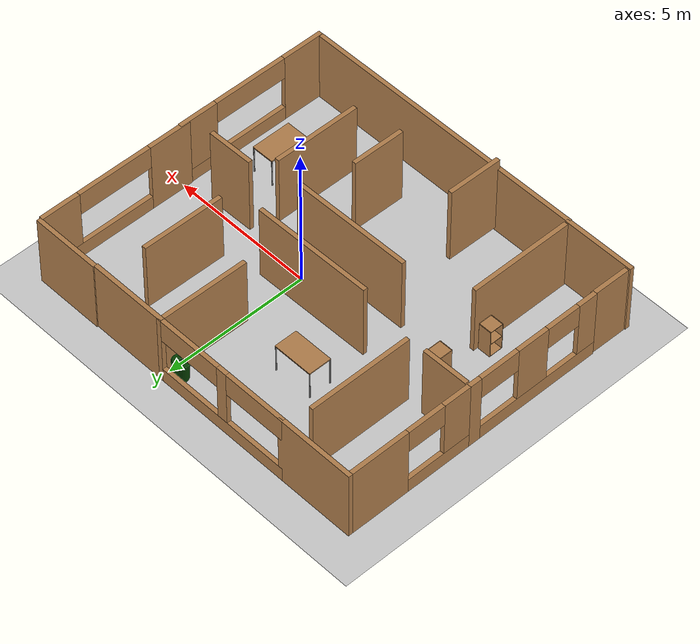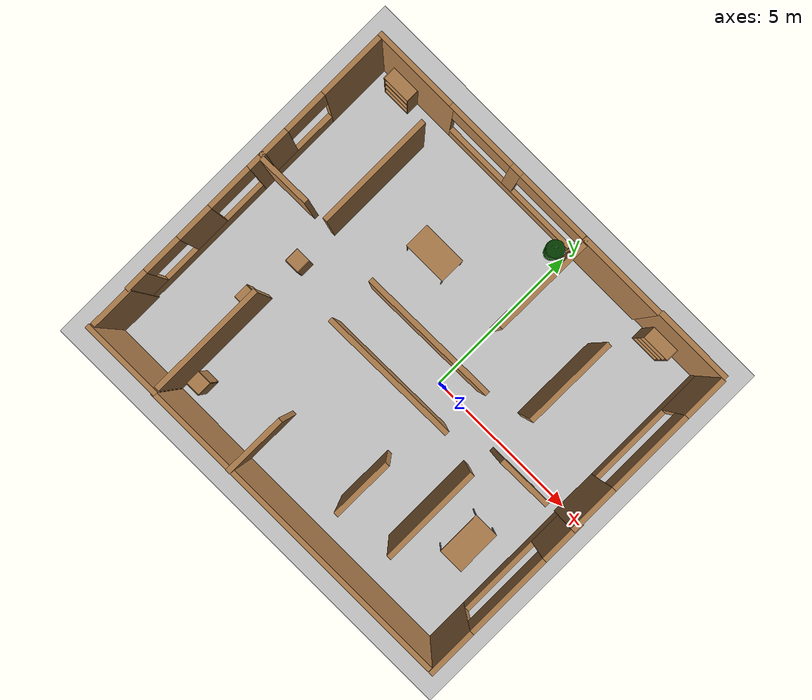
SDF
<?xml version="1.0"?>
<sdf version="1.6">
  <world name="default">

    <include>
      <uri>model://ground_plane</uri>
    </include>

    <include>
      <uri>model://sun</uri>
    </include>

    <scene>
      <shadows>false</shadows>
    </scene>

    <gui fullscreen='0'>
      <camera name='user_camera'>
        <pose frame=''>0.319654 -0.235002 9.29441 0 1.5138 0.009599</pose>
        <view_controller>orbit</view_controller>
        <projection_type>perspective</projection_type>
      </camera>
    </gui>

    <physics type="ode">
      <real_time_update_rate>1000.0</real_time_update_rate>
      <max_step_size>0.001</max_step_size>
      <real_time_factor>1</real_time_factor>
      <ode>
        <solver>
          <type>quick</type>
          <iters>150</iters>
          <precon_iters>0</precon_iters>
          <sor>1.400000</sor>
          <use_dynamic_moi_rescaling>1</use_dynamic_moi_rescaling>
        </solver>
        <constraints>
          <cfm>0.00001</cfm>
          <erp>0.2</erp>
          <contact_max_correcting_vel>2000.000000</contact_max_correcting_vel>
          <contact_surface_layer>0.01000</contact_surface_layer>
        </constraints>
      </ode>
    </physics>

    <model name="world">
      <static>1</static>
      <include>
        <uri>model://world</uri>
      </include>
    </model>

  </world>
</sdf>

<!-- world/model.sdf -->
<sdf version='1.7'>
  <model name='world'>
    <link name='Wall_81'>
      <pose>3.81216 5.30314 0 0 -0 3.14159</pose>
      <self_collide>0</self_collide>
      <kinematic>0</kinematic>
      <enable_wind>0</enable_wind>
      <inertial>
        <inertia>
          <ixx>0</ixx>
          <ixy>0</ixy>
          <ixz>0</ixz>
          <iyy>0</iyy>
          <iyz>0</iyz>
          <izz>0</izz>
        </inertia>
        <mass>0</mass>
        <pose>0 0 0 0 -0 0</pose>
      </inertial>
      <visual name='Wall_81_Visual'>
        <pose>0 0 1.25 0 -0 0</pose>
        <geometry>
          <box>
            <size>2.39676 0.15 2.5</size>
          </box>
        </geometry>
        <material>
          <script>
            <uri>file://media/materials/scripts/gazebo.material</uri>
            <name>Gazebo/Wood</name>
          </script>
          <ambient>1 1 1 1</ambient>
          <diffuse>1 1 1 1</diffuse>
          <specular>0.2 0.2 0.2 1</specular>
          <emissive>0 0 0 1</emissive>
          <shader type='pixel'/>
        </material>
        <cast_shadows>1</cast_shadows>
        <transparency>0</transparency>
      </visual>
      <collision name='Wall_81_Collision'>
        <laser_retro>0</laser_retro>
        <max_contacts>10</max_contacts>
        <pose>0 0 1.25 0 -0 0</pose>
        <geometry>
          <box>
            <size>2.39676 0.15 2.5</size>
          </box>
        </geometry>
        <surface>
          <friction>
            <ode>
              <mu>1</mu>
              <mu2>1</mu2>
              <fdir1>0 0 0</fdir1>
              <slip1>0</slip1>
              <slip2>0</slip2>
            </ode>
            <torsional>
              <coefficient>1</coefficient>
              <patch_radius>0</patch_radius>
              <surface_radius>0</surface_radius>
              <use_patch_radius>1</use_patch_radius>
              <ode>
                <slip>0</slip>
              </ode>
            </torsional>
          </friction>
          <bounce>
            <restitution_coefficient>0</restitution_coefficient>
            <threshold>1e+06</threshold>
          </bounce>
          <contact>
            <collide_without_contact>0</collide_without_contact>
            <collide_without_contact_bitmask>1</collide_without_contact_bitmask>
            <collide_bitmask>1</collide_bitmask>
            <ode>
              <soft_cfm>0</soft_cfm>
              <soft_erp>0.2</soft_erp>
              <kp>1e+13</kp>
              <kd>1</kd>
              <max_vel>0.01</max_vel>
              <min_depth>0</min_depth>
            </ode>
            <bullet>
              <split_impulse>1</split_impulse>
              <split_impulse_penetration_threshold>-0.01</split_impulse_penetration_threshold>
              <soft_cfm>0</soft_cfm>
              <soft_erp>0.2</soft_erp>
              <kp>1e+13</kp>
              <kd>1</kd>
            </bullet>
          </contact>
        </surface>
      </collision>
    </link>
    <link name='Wall_82'>
      <pose>1.25 5.26876 0 0 -0 3.14159</pose>
      <self_collide>0</self_collide>
      <kinematic>0</kinematic>
      <enable_wind>0</enable_wind>
      <visual name='Wall_82_Visual'>
        <pose>0 0 1.25 0 -0 0</pose>
        <geometry>
          <box>
            <size>2.75 0.15 2.5</size>
          </box>
        </geometry>
        <material>
          <script>
            <uri>file://media/materials/scripts/gazebo.material</uri>
            <name>Gazebo/Wood</name>
          </script>
          <ambient>1 1 1 1</ambient>
          <diffuse>1 1 1 1</diffuse>
          <specular>0.2 0.2 0.2 1</specular>
          <emissive>0 0 0 1</emissive>
          <shader type='pixel'/>
        </material>
        <cast_shadows>1</cast_shadows>
        <transparency>0</transparency>
      </visual>
      <collision name='Wall_82_Collision'>
        <laser_retro>0</laser_retro>
        <max_contacts>10</max_contacts>
        <pose>0 0 1.25 0 -0 0</pose>
        <geometry>
          <box>
            <size>2.75 0.15 2.5</size>
          </box>
        </geometry>
        <surface>
          <friction>
            <ode>
              <mu>1</mu>
              <mu2>1</mu2>
              <fdir1>0 0 0</fdir1>
              <slip1>0</slip1>
              <slip2>0</slip2>
            </ode>
            <torsional>
              <coefficient>1</coefficient>
              <patch_radius>0</patch_radius>
              <surface_radius>0</surface_radius>
              <use_patch_radius>1</use_patch_radius>
              <ode>
                <slip>0</slip>
              </ode>
            </torsional>
          </friction>
          <bounce>
            <restitution_coefficient>0</restitution_coefficient>
            <threshold>1e+06</threshold>
          </bounce>
          <contact>
            <collide_without_contact>0</collide_without_contact>
            <collide_without_contact_bitmask>1</collide_without_contact_bitmask>
            <collide_bitmask>1</collide_bitmask>
            <ode>
              <soft_cfm>0</soft_cfm>
              <soft_erp>0.2</soft_erp>
              <kp>1e+13</kp>
              <kd>1</kd>
              <max_vel>0.01</max_vel>
              <min_depth>0</min_depth>
            </ode>
            <bullet>
              <split_impulse>1</split_impulse>
              <split_impulse_penetration_threshold>-0.01</split_impulse_penetration_threshold>
              <soft_cfm>0</soft_cfm>
              <soft_erp>0.2</soft_erp>
              <kp>1e+13</kp>
              <kd>1</kd>
            </bullet>
          </contact>
        </surface>
      </collision>
    </link>
    <link name='Wall_83'>
      <pose>-2.475 5.275 0 0 -0 3.14159</pose>
      <self_collide>0</self_collide>
      <kinematic>0</kinematic>
      <enable_wind>0</enable_wind>
      <inertial>
        <inertia>
          <ixx>0</ixx>
          <ixy>0</ixy>
          <ixz>0</ixz>
          <iyy>0</iyy>
          <iyz>0</iyz>
          <izz>0</izz>
        </inertia>
        <mass>0</mass>
        <pose>0 0 0 0 -0 0</pose>
      </inertial>
      <visual name='Wall_83_Visual_5'>
        <pose>1.39775 0 2.1 0 -0 0</pose>
        <geometry>
          <box>
            <size>2.20449 0.15 0.8</size>
          </box>
        </geometry>
        <material>
          <script>
            <uri>file://media/materials/scripts/gazebo.material</uri>
            <name>Gazebo/Wood</name>
          </script>
          <ambient>1 1 1 1</ambient>
          <diffuse>1 1 1 1</diffuse>
          <specular>0.2 0.2 0.2 1</specular>
          <emissive>0 0 0 1</emissive>
          <shader type='pixel'/>
        </material>
        <cast_shadows>1</cast_shadows>
        <transparency>0</transparency>
      </visual>
      <visual name='Wall_83_Visual_2'>
        <pose>0.110246 0 1.5 0 -0 0</pose>
        <geometry>
          <box>
            <size>0.37052 0.15 2</size>
          </box>
        </geometry>
        <material>
          <script>
            <uri>file://media/materials/scripts/gazebo.material</uri>
            <name>Gazebo/Wood</name>
          </script>
          <ambient>1 1 1 1</ambient>
          <diffuse>1 1 1 1</diffuse>
          <specular>0.2 0.2 0.2 1</specular>
          <emissive>0 0 0 1</emissive>
          <shader type='pixel'/>
        </material>
        <cast_shadows>1</cast_shadows>
        <transparency>0</transparency>
      </visual>
      <visual name='Wall_83_Visual_6'>
        <pose>1.39775 0 2.1 0 -0 0</pose>
        <geometry>
          <box>
            <size>2.20449 0.15 0.8</size>
          </box>
        </geometry>
        <material>
          <script>
            <uri>file://media/materials/scripts/gazebo.material</uri>
            <name>Gazebo/Wood</name>
          </script>
          <ambient>1 1 1 1</ambient>
          <diffuse>1 1 1 1</diffuse>
          <specular>0.2 0.2 0.2 1</specular>
          <emissive>0 0 0 1</emissive>
          <shader type='pixel'/>
        </material>
        <cast_shadows>1</cast_shadows>
        <transparency>0</transparency>
      </visual>
      <visual name='Wall_83_Visual_3'>
        <pose>0.110246 0 1.5 0 -0 0</pose>
        <geometry>
          <box>
            <size>0.37052 0.15 2</size>
          </box>
        </geometry>
        <material>
          <script>
            <uri>file://media/materials/scripts/gazebo.material</uri>
            <name>Gazebo/Wood</name>
          </script>
          <ambient>1 1 1 1</ambient>
          <diffuse>1 1 1 1</diffuse>
          <specular>0.2 0.2 0.2 1</specular>
          <emissive>0 0 0 1</emissive>
          <shader type='pixel'/>
        </material>
        <cast_shadows>1</cast_shadows>
        <transparency>0</transparency>
      </visual>
      <visual name='Wall_83_Visual_4'>
        <pose>-1.20651 0 2.1 0 -0 0</pose>
        <geometry>
          <box>
            <size>2.263 0.15 0.8</size>
          </box>
        </geometry>
        <material>
          <script>
            <uri>file://media/materials/scripts/gazebo.material</uri>
            <name>Gazebo/Wood</name>
          </script>
          <ambient>1 1 1 1</ambient>
          <diffuse>1 1 1 1</diffuse>
          <specular>0.2 0.2 0.2 1</specular>
          <emissive>0 0 0 1</emissive>
          <shader type='pixel'/>
        </material>
        <cast_shadows>1</cast_shadows>
        <transparency>0</transparency>
      </visual>
      <visual name='Wall_83_Visual_1'>
        <pose>0.080993 0 0.25 0 -0 0</pose>
        <geometry>
          <box>
            <size>4.83801 0.15 0.5</size>
          </box>
        </geometry>
        <material>
          <script>
            <uri>file://media/materials/scripts/gazebo.material</uri>
            <name>Gazebo/Wood</name>
          </script>
          <ambient>1 1 1 1</ambient>
          <diffuse>1 1 1 1</diffuse>
          <specular>0.2 0.2 0.2 1</specular>
          <emissive>0 0 0 1</emissive>
          <shader type='pixel'/>
        </material>
        <cast_shadows>1</cast_shadows>
        <transparency>0</transparency>
      </visual>
      <visual name='Wall_83_Visual_0'>
        <pose>-2.41901 0 1.25 0 -0 0</pose>
        <geometry>
          <box>
            <size>0.161986 0.15 2.5</size>
          </box>
        </geometry>
        <material>
          <script>
            <uri>file://media/materials/scripts/gazebo.material</uri>
            <name>Gazebo/Wood</name>
          </script>
          <ambient>1 1 1 1</ambient>
          <diffuse>1 1 1 1</diffuse>
          <specular>0.2 0.2 0.2 1</specular>
          <emissive>0 0 0 1</emissive>
          <shader type='pixel'/>
        </material>
        <cast_shadows>1</cast_shadows>
        <transparency>0</transparency>
      </visual>
      <collision name='Wall_83_Collision_4'>
        <laser_retro>0</laser_retro>
        <max_contacts>10</max_contacts>
        <pose>-1.20651 0 2.1 0 -0 0</pose>
        <geometry>
          <box>
            <size>2.263 0.15 0.8</size>
          </box>
        </geometry>
        <surface>
          <friction>
            <ode>
              <mu>1</mu>
              <mu2>1</mu2>
              <fdir1>0 0 0</fdir1>
              <slip1>0</slip1>
              <slip2>0</slip2>
            </ode>
            <torsional>
              <coefficient>1</coefficient>
              <patch_radius>0</patch_radius>
              <surface_radius>0</surface_radius>
              <use_patch_radius>1</use_patch_radius>
              <ode>
                <slip>0</slip>
              </ode>
            </torsional>
          </friction>
          <bounce>
            <restitution_coefficient>0</restitution_coefficient>
            <threshold>1e+06</threshold>
          </bounce>
          <contact>
            <collide_without_contact>0</collide_without_contact>
            <collide_without_contact_bitmask>1</collide_without_contact_bitmask>
            <collide_bitmask>1</collide_bitmask>
            <ode>
              <soft_cfm>0</soft_cfm>
              <soft_erp>0.2</soft_erp>
              <kp>1e+13</kp>
              <kd>1</kd>
              <max_vel>0.01</max_vel>
              <min_depth>0</min_depth>
            </ode>
            <bullet>
              <split_impulse>1</split_impulse>
              <split_impulse_penetration_threshold>-0.01</split_impulse_penetration_threshold>
              <soft_cfm>0</soft_cfm>
              <soft_erp>0.2</soft_erp>
              <kp>1e+13</kp>
              <kd>1</kd>
            </bullet>
          </contact>
        </surface>
      </collision>
      <collision name='Wall_83_Collision_6'>
        <laser_retro>0</laser_retro>
        <max_contacts>10</max_contacts>
        <pose>1.39775 0 2.1 0 -0 0</pose>
        <geometry>
          <box>
            <size>2.20449 0.15 0.8</size>
          </box>
        </geometry>
        <surface>
          <friction>
            <ode>
              <mu>1</mu>
              <mu2>1</mu2>
              <fdir1>0 0 0</fdir1>
              <slip1>0</slip1>
              <slip2>0</slip2>
            </ode>
            <torsional>
              <coefficient>1</coefficient>
              <patch_radius>0</patch_radius>
              <surface_radius>0</surface_radius>
              <use_patch_radius>1</use_patch_radius>
              <ode>
                <slip>0</slip>
              </ode>
            </torsional>
          </friction>
          <bounce>
            <restitution_coefficient>0</restitution_coefficient>
            <threshold>1e+06</threshold>
          </bounce>
          <contact>
            <collide_without_contact>0</collide_without_contact>
            <collide_without_contact_bitmask>1</collide_without_contact_bitmask>
            <collide_bitmask>1</collide_bitmask>
            <ode>
              <soft_cfm>0</soft_cfm>
              <soft_erp>0.2</soft_erp>
              <kp>1e+13</kp>
              <kd>1</kd>
              <max_vel>0.01</max_vel>
              <min_depth>0</min_depth>
            </ode>
            <bullet>
              <split_impulse>1</split_impulse>
              <split_impulse_penetration_threshold>-0.01</split_impulse_penetration_threshold>
              <soft_cfm>0</soft_cfm>
              <soft_erp>0.2</soft_erp>
              <kp>1e+13</kp>
              <kd>1</kd>
            </bullet>
          </contact>
        </surface>
      </collision>
      <collision name='Wall_83_Collision_2'>
        <laser_retro>0</laser_retro>
        <max_contacts>10</max_contacts>
        <pose>0.110246 0 1.5 0 -0 0</pose>
        <geometry>
          <box>
            <size>0.37052 0.15 2</size>
          </box>
        </geometry>
        <surface>
          <friction>
            <ode>
              <mu>1</mu>
              <mu2>1</mu2>
              <fdir1>0 0 0</fdir1>
              <slip1>0</slip1>
              <slip2>0</slip2>
            </ode>
            <torsional>
              <coefficient>1</coefficient>
              <patch_radius>0</patch_radius>
              <surface_radius>0</surface_radius>
              <use_patch_radius>1</use_patch_radius>
              <ode>
                <slip>0</slip>
              </ode>
            </torsional>
          </friction>
          <bounce>
            <restitution_coefficient>0</restitution_coefficient>
            <threshold>1e+06</threshold>
          </bounce>
          <contact>
            <collide_without_contact>0</collide_without_contact>
            <collide_without_contact_bitmask>1</collide_without_contact_bitmask>
            <collide_bitmask>1</collide_bitmask>
            <ode>
              <soft_cfm>0</soft_cfm>
              <soft_erp>0.2</soft_erp>
              <kp>1e+13</kp>
              <kd>1</kd>
              <max_vel>0.01</max_vel>
              <min_depth>0</min_depth>
            </ode>
            <bullet>
              <split_impulse>1</split_impulse>
              <split_impulse_penetration_threshold>-0.01</split_impulse_penetration_threshold>
              <soft_cfm>0</soft_cfm>
              <soft_erp>0.2</soft_erp>
              <kp>1e+13</kp>
              <kd>1</kd>
            </bullet>
          </contact>
        </surface>
      </collision>
      <collision name='Wall_83_Collision_0'>
        <laser_retro>0</laser_retro>
        <max_contacts>10</max_contacts>
        <pose>-2.41901 0 1.25 0 -0 0</pose>
        <geometry>
          <box>
            <size>0.161986 0.15 2.5</size>
          </box>
        </geometry>
        <surface>
          <friction>
            <ode>
              <mu>1</mu>
              <mu2>1</mu2>
              <fdir1>0 0 0</fdir1>
              <slip1>0</slip1>
              <slip2>0</slip2>
            </ode>
            <torsional>
              <coefficient>1</coefficient>
              <patch_radius>0</patch_radius>
              <surface_radius>0</surface_radius>
              <use_patch_radius>1</use_patch_radius>
              <ode>
                <slip>0</slip>
              </ode>
            </torsional>
          </friction>
          <bounce>
            <restitution_coefficient>0</restitution_coefficient>
            <threshold>1e+06</threshold>
          </bounce>
          <contact>
            <collide_without_contact>0</collide_without_contact>
            <collide_without_contact_bitmask>1</collide_without_contact_bitmask>
            <collide_bitmask>1</collide_bitmask>
            <ode>
              <soft_cfm>0</soft_cfm>
              <soft_erp>0.2</soft_erp>
              <kp>1e+13</kp>
              <kd>1</kd>
              <max_vel>0.01</max_vel>
              <min_depth>0</min_depth>
            </ode>
            <bullet>
              <split_impulse>1</split_impulse>
              <split_impulse_penetration_threshold>-0.01</split_impulse_penetration_threshold>
              <soft_cfm>0</soft_cfm>
              <soft_erp>0.2</soft_erp>
              <kp>1e+13</kp>
              <kd>1</kd>
            </bullet>
          </contact>
        </surface>
      </collision>
      <collision name='Wall_83_Collision_1'>
        <laser_retro>0</laser_retro>
        <max_contacts>10</max_contacts>
        <pose>0.080993 0 0.25 0 -0 0</pose>
        <geometry>
          <box>
            <size>4.83801 0.15 0.5</size>
          </box>
        </geometry>
        <surface>
          <friction>
            <ode>
              <mu>1</mu>
              <mu2>1</mu2>
              <fdir1>0 0 0</fdir1>
              <slip1>0</slip1>
              <slip2>0</slip2>
            </ode>
            <torsional>
              <coefficient>1</coefficient>
              <patch_radius>0</patch_radius>
              <surface_radius>0</surface_radius>
              <use_patch_radius>1</use_patch_radius>
              <ode>
                <slip>0</slip>
              </ode>
            </torsional>
          </friction>
          <bounce>
            <restitution_coefficient>0</restitution_coefficient>
            <threshold>1e+06</threshold>
          </bounce>
          <contact>
            <collide_without_contact>0</collide_without_contact>
            <collide_without_contact_bitmask>1</collide_without_contact_bitmask>
            <collide_bitmask>1</collide_bitmask>
            <ode>
              <soft_cfm>0</soft_cfm>
              <soft_erp>0.2</soft_erp>
              <kp>1e+13</kp>
              <kd>1</kd>
              <max_vel>0.01</max_vel>
              <min_depth>0</min_depth>
            </ode>
            <bullet>
              <split_impulse>1</split_impulse>
              <split_impulse_penetration_threshold>-0.01</split_impulse_penetration_threshold>
              <soft_cfm>0</soft_cfm>
              <soft_erp>0.2</soft_erp>
              <kp>1e+13</kp>
              <kd>1</kd>
            </bullet>
          </contact>
        </surface>
      </collision>
      <collision name='Wall_83_Collision_3'>
        <laser_retro>0</laser_retro>
        <max_contacts>10</max_contacts>
        <pose>0.110246 0 1.5 0 -0 0</pose>
        <geometry>
          <box>
            <size>0.37052 0.15 2</size>
          </box>
        </geometry>
        <surface>
          <friction>
            <ode>
              <mu>1</mu>
              <mu2>1</mu2>
              <fdir1>0 0 0</fdir1>
              <slip1>0</slip1>
              <slip2>0</slip2>
            </ode>
            <torsional>
              <coefficient>1</coefficient>
              <patch_radius>0</patch_radius>
              <surface_radius>0</surface_radius>
              <use_patch_radius>1</use_patch_radius>
              <ode>
                <slip>0</slip>
              </ode>
            </torsional>
          </friction>
          <bounce>
            <restitution_coefficient>0</restitution_coefficient>
            <threshold>1e+06</threshold>
          </bounce>
          <contact>
            <collide_without_contact>0</collide_without_contact>
            <collide_without_contact_bitmask>1</collide_without_contact_bitmask>
            <collide_bitmask>1</collide_bitmask>
            <ode>
              <soft_cfm>0</soft_cfm>
              <soft_erp>0.2</soft_erp>
              <kp>1e+13</kp>
              <kd>1</kd>
              <max_vel>0.01</max_vel>
              <min_depth>0</min_depth>
            </ode>
            <bullet>
              <split_impulse>1</split_impulse>
              <split_impulse_penetration_threshold>-0.01</split_impulse_penetration_threshold>
              <soft_cfm>0</soft_cfm>
              <soft_erp>0.2</soft_erp>
              <kp>1e+13</kp>
              <kd>1</kd>
            </bullet>
          </contact>
        </surface>
      </collision>
      <collision name='Wall_83_Collision_5'>
        <laser_retro>0</laser_retro>
        <max_contacts>10</max_contacts>
        <pose>1.39775 0 2.1 0 -0 0</pose>
        <geometry>
          <box>
            <size>2.20449 0.15 0.8</size>
          </box>
        </geometry>
        <surface>
          <friction>
            <ode>
              <mu>1</mu>
              <mu2>1</mu2>
              <fdir1>0 0 0</fdir1>
              <slip1>0</slip1>
              <slip2>0</slip2>
            </ode>
            <torsional>
              <coefficient>1</coefficient>
              <patch_radius>0</patch_radius>
              <surface_radius>0</surface_radius>
              <use_patch_radius>1</use_patch_radius>
              <ode>
                <slip>0</slip>
              </ode>
            </torsional>
          </friction>
          <bounce>
            <restitution_coefficient>0</restitution_coefficient>
            <threshold>1e+06</threshold>
          </bounce>
          <contact>
            <collide_without_contact>0</collide_without_contact>
            <collide_without_contact_bitmask>1</collide_without_contact_bitmask>
            <collide_bitmask>1</collide_bitmask>
            <ode>
              <soft_cfm>0</soft_cfm>
              <soft_erp>0.2</soft_erp>
              <kp>1e+13</kp>
              <kd>1</kd>
              <max_vel>0.01</max_vel>
              <min_depth>0</min_depth>
            </ode>
            <bullet>
              <split_impulse>1</split_impulse>
              <split_impulse_penetration_threshold>-0.01</split_impulse_penetration_threshold>
              <soft_cfm>0</soft_cfm>
              <soft_erp>0.2</soft_erp>
              <kp>1e+13</kp>
              <kd>1</kd>
            </bullet>
          </contact>
        </surface>
      </collision>
    </link>
    <link name='Wall_84'>
      <pose>-6.2 5.275 0 0 -0 3.14159</pose>
      <self_collide>0</self_collide>
      <kinematic>0</kinematic>
      <enable_wind>0</enable_wind>
      <visual name='Wall_84_Visual'>
        <pose>0 0 1.25 0 -0 0</pose>
        <geometry>
          <box>
            <size>2.75 0.15 2.5</size>
          </box>
        </geometry>
        <material>
          <script>
            <uri>file://media/materials/scripts/gazebo.material</uri>
            <name>Gazebo/Wood</name>
          </script>
          <ambient>1 1 1 1</ambient>
          <diffuse>1 1 1 1</diffuse>
          <specular>0.2 0.2 0.2 1</specular>
          <emissive>0 0 0 1</emissive>
          <shader type='pixel'/>
        </material>
        <cast_shadows>1</cast_shadows>
        <transparency>0</transparency>
      </visual>
      <collision name='Wall_84_Collision'>
        <laser_retro>0</laser_retro>
        <max_contacts>10</max_contacts>
        <pose>0 0 1.25 0 -0 0</pose>
        <geometry>
          <box>
            <size>2.75 0.15 2.5</size>
          </box>
        </geometry>
        <surface>
          <friction>
            <ode>
              <mu>1</mu>
              <mu2>1</mu2>
              <fdir1>0 0 0</fdir1>
              <slip1>0</slip1>
              <slip2>0</slip2>
            </ode>
            <torsional>
              <coefficient>1</coefficient>
              <patch_radius>0</patch_radius>
              <surface_radius>0</surface_radius>
              <use_patch_radius>1</use_patch_radius>
              <ode>
                <slip>0</slip>
              </ode>
            </torsional>
          </friction>
          <bounce>
            <restitution_coefficient>0</restitution_coefficient>
            <threshold>1e+06</threshold>
          </bounce>
          <contact>
            <collide_without_contact>0</collide_without_contact>
            <collide_without_contact_bitmask>1</collide_without_contact_bitmask>
            <collide_bitmask>1</collide_bitmask>
            <ode>
              <soft_cfm>0</soft_cfm>
              <soft_erp>0.2</soft_erp>
              <kp>1e+13</kp>
              <kd>1</kd>
              <max_vel>0.01</max_vel>
              <min_depth>0</min_depth>
            </ode>
            <bullet>
              <split_impulse>1</split_impulse>
              <split_impulse_penetration_threshold>-0.01</split_impulse_penetration_threshold>
              <soft_cfm>0</soft_cfm>
              <soft_erp>0.2</soft_erp>
              <kp>1e+13</kp>
              <kd>1</kd>
            </bullet>
          </contact>
        </surface>
      </collision>
    </link>
    <link name='Wall_85'>
      <pose>-7.5 3.1 0 0 0 -1.5708</pose>
      <self_collide>0</self_collide>
      <kinematic>0</kinematic>
      <enable_wind>0</enable_wind>
      <visual name='Wall_85_Visual_3'>
        <pose>0.62212 0 2.1 0 -0 0</pose>
        <geometry>
          <box>
            <size>1.332 0.15 0.8</size>
          </box>
        </geometry>
        <material>
          <script>
            <uri>file://media/materials/scripts/gazebo.material</uri>
            <name>Gazebo/Wood</name>
          </script>
          <ambient>1 1 1 1</ambient>
          <diffuse>1 1 1 1</diffuse>
          <specular>0.2 0.2 0.2 1</specular>
          <emissive>0 0 0 1</emissive>
          <shader type='pixel'/>
        </material>
        <cast_shadows>1</cast_shadows>
        <transparency>0</transparency>
      </visual>
      <visual name='Wall_85_Visual_2'>
        <pose>1.76906 0 1.5 0 -0 0</pose>
        <geometry>
          <box>
            <size>0.96188 0.15 2</size>
          </box>
        </geometry>
        <material>
          <script>
            <uri>file://media/materials/scripts/gazebo.material</uri>
            <name>Gazebo/Wood</name>
          </script>
          <ambient>1 1 1 1</ambient>
          <diffuse>1 1 1 1</diffuse>
          <specular>0.2 0.2 0.2 1</specular>
          <emissive>0 0 0 1</emissive>
          <shader type='pixel'/>
        </material>
        <cast_shadows>1</cast_shadows>
        <transparency>0</transparency>
      </visual>
      <visual name='Wall_85_Visual_0'>
        <pose>-1.14694 0 1.25 0 -0 0</pose>
        <geometry>
          <box>
            <size>2.20612 0.15 2.5</size>
          </box>
        </geometry>
        <material>
          <script>
            <uri>file://media/materials/scripts/gazebo.material</uri>
            <name>Gazebo/Wood</name>
          </script>
          <ambient>1 1 1 1</ambient>
          <diffuse>1 1 1 1</diffuse>
          <specular>0.2 0.2 0.2 1</specular>
          <emissive>0 0 0 1</emissive>
          <shader type='pixel'/>
        </material>
        <cast_shadows>1</cast_shadows>
        <transparency>0</transparency>
      </visual>
      <visual name='Wall_85_Visual_1'>
        <pose>1.10306 0 0.25 0 -0 0</pose>
        <geometry>
          <box>
            <size>2.29388 0.15 0.5</size>
          </box>
        </geometry>
        <material>
          <script>
            <uri>file://media/materials/scripts/gazebo.material</uri>
            <name>Gazebo/Wood</name>
          </script>
          <ambient>1 1 1 1</ambient>
          <diffuse>1 1 1 1</diffuse>
          <specular>0.2 0.2 0.2 1</specular>
          <emissive>0 0 0 1</emissive>
          <shader type='pixel'/>
        </material>
        <cast_shadows>1</cast_shadows>
        <transparency>0</transparency>
      </visual>
      <collision name='Wall_85_Collision_3'>
        <laser_retro>0</laser_retro>
        <max_contacts>10</max_contacts>
        <pose>0.62212 0 2.1 0 -0 0</pose>
        <geometry>
          <box>
            <size>1.332 0.15 0.8</size>
          </box>
        </geometry>
        <surface>
          <friction>
            <ode>
              <mu>1</mu>
              <mu2>1</mu2>
              <fdir1>0 0 0</fdir1>
              <slip1>0</slip1>
              <slip2>0</slip2>
            </ode>
            <torsional>
              <coefficient>1</coefficient>
              <patch_radius>0</patch_radius>
              <surface_radius>0</surface_radius>
              <use_patch_radius>1</use_patch_radius>
              <ode>
                <slip>0</slip>
              </ode>
            </torsional>
          </friction>
          <bounce>
            <restitution_coefficient>0</restitution_coefficient>
            <threshold>1e+06</threshold>
          </bounce>
          <contact>
            <collide_without_contact>0</collide_without_contact>
            <collide_without_contact_bitmask>1</collide_without_contact_bitmask>
            <collide_bitmask>1</collide_bitmask>
            <ode>
              <soft_cfm>0</soft_cfm>
              <soft_erp>0.2</soft_erp>
              <kp>1e+13</kp>
              <kd>1</kd>
              <max_vel>0.01</max_vel>
              <min_depth>0</min_depth>
            </ode>
            <bullet>
              <split_impulse>1</split_impulse>
              <split_impulse_penetration_threshold>-0.01</split_impulse_penetration_threshold>
              <soft_cfm>0</soft_cfm>
              <soft_erp>0.2</soft_erp>
              <kp>1e+13</kp>
              <kd>1</kd>
            </bullet>
          </contact>
        </surface>
      </collision>
      <collision name='Wall_85_Collision_0'>
        <laser_retro>0</laser_retro>
        <max_contacts>10</max_contacts>
        <pose>-1.14694 0 1.25 0 -0 0</pose>
        <geometry>
          <box>
            <size>2.20612 0.15 2.5</size>
          </box>
        </geometry>
        <surface>
          <friction>
            <ode>
              <mu>1</mu>
              <mu2>1</mu2>
              <fdir1>0 0 0</fdir1>
              <slip1>0</slip1>
              <slip2>0</slip2>
            </ode>
            <torsional>
              <coefficient>1</coefficient>
              <patch_radius>0</patch_radius>
              <surface_radius>0</surface_radius>
              <use_patch_radius>1</use_patch_radius>
              <ode>
                <slip>0</slip>
              </ode>
            </torsional>
          </friction>
          <bounce>
            <restitution_coefficient>0</restitution_coefficient>
            <threshold>1e+06</threshold>
          </bounce>
          <contact>
            <collide_without_contact>0</collide_without_contact>
            <collide_without_contact_bitmask>1</collide_without_contact_bitmask>
            <collide_bitmask>1</collide_bitmask>
            <ode>
              <soft_cfm>0</soft_cfm>
              <soft_erp>0.2</soft_erp>
              <kp>1e+13</kp>
              <kd>1</kd>
              <max_vel>0.01</max_vel>
              <min_depth>0</min_depth>
            </ode>
            <bullet>
              <split_impulse>1</split_impulse>
              <split_impulse_penetration_threshold>-0.01</split_impulse_penetration_threshold>
              <soft_cfm>0</soft_cfm>
              <soft_erp>0.2</soft_erp>
              <kp>1e+13</kp>
              <kd>1</kd>
            </bullet>
          </contact>
        </surface>
      </collision>
      <collision name='Wall_85_Collision_2'>
        <laser_retro>0</laser_retro>
        <max_contacts>10</max_contacts>
        <pose>1.76906 0 1.5 0 -0 0</pose>
        <geometry>
          <box>
            <size>0.96188 0.15 2</size>
          </box>
        </geometry>
        <surface>
          <friction>
            <ode>
              <mu>1</mu>
              <mu2>1</mu2>
              <fdir1>0 0 0</fdir1>
              <slip1>0</slip1>
              <slip2>0</slip2>
            </ode>
            <torsional>
              <coefficient>1</coefficient>
              <patch_radius>0</patch_radius>
              <surface_radius>0</surface_radius>
              <use_patch_radius>1</use_patch_radius>
              <ode>
                <slip>0</slip>
              </ode>
            </torsional>
          </friction>
          <bounce>
            <restitution_coefficient>0</restitution_coefficient>
            <threshold>1e+06</threshold>
          </bounce>
          <contact>
            <collide_without_contact>0</collide_without_contact>
            <collide_without_contact_bitmask>1</collide_without_contact_bitmask>
            <collide_bitmask>1</collide_bitmask>
            <ode>
              <soft_cfm>0</soft_cfm>
              <soft_erp>0.2</soft_erp>
              <kp>1e+13</kp>
              <kd>1</kd>
              <max_vel>0.01</max_vel>
              <min_depth>0</min_depth>
            </ode>
            <bullet>
              <split_impulse>1</split_impulse>
              <split_impulse_penetration_threshold>-0.01</split_impulse_penetration_threshold>
              <soft_cfm>0</soft_cfm>
              <soft_erp>0.2</soft_erp>
              <kp>1e+13</kp>
              <kd>1</kd>
            </bullet>
          </contact>
        </surface>
      </collision>
      <collision name='Wall_85_Collision_1'>
        <laser_retro>0</laser_retro>
        <max_contacts>10</max_contacts>
        <pose>1.10306 0 0.25 0 -0 0</pose>
        <geometry>
          <box>
            <size>2.29388 0.15 0.5</size>
          </box>
        </geometry>
        <surface>
          <friction>
            <ode>
              <mu>1</mu>
              <mu2>1</mu2>
              <fdir1>0 0 0</fdir1>
              <slip1>0</slip1>
              <slip2>0</slip2>
            </ode>
            <torsional>
              <coefficient>1</coefficient>
              <patch_radius>0</patch_radius>
              <surface_radius>0</surface_radius>
              <use_patch_radius>1</use_patch_radius>
              <ode>
                <slip>0</slip>
              </ode>
            </torsional>
          </friction>
          <bounce>
            <restitution_coefficient>0</restitution_coefficient>
            <threshold>1e+06</threshold>
          </bounce>
          <contact>
            <collide_without_contact>0</collide_without_contact>
            <collide_without_contact_bitmask>1</collide_without_contact_bitmask>
            <collide_bitmask>1</collide_bitmask>
            <ode>
              <soft_cfm>0</soft_cfm>
              <soft_erp>0.2</soft_erp>
              <kp>1e+13</kp>
              <kd>1</kd>
              <max_vel>0.01</max_vel>
              <min_depth>0</min_depth>
            </ode>
            <bullet>
              <split_impulse>1</split_impulse>
              <split_impulse_penetration_threshold>-0.01</split_impulse_penetration_threshold>
              <soft_cfm>0</soft_cfm>
              <soft_erp>0.2</soft_erp>
              <kp>1e+13</kp>
              <kd>1</kd>
            </bullet>
          </contact>
        </surface>
      </collision>
    </link>
    <link name='Wall_86'>
      <pose>-7.5 -1.5 0 0 0 -1.5708</pose>
      <self_collide>0</self_collide>
      <kinematic>0</kinematic>
      <enable_wind>0</enable_wind>
      <visual name='Wall_86_Visual_1'>
        <pose>0.28462 0 0.25 0 -0 0</pose>
        <geometry>
          <box>
            <size>4.43076 0.15 0.5</size>
          </box>
        </geometry>
        <material>
          <script>
            <uri>file://media/materials/scripts/gazebo.material</uri>
            <name>Gazebo/Wood</name>
          </script>
          <ambient>1 1 1 1</ambient>
          <diffuse>1 1 1 1</diffuse>
          <specular>0.2 0.2 0.2 1</specular>
          <emissive>0 0 0 1</emissive>
          <shader type='pixel'/>
        </material>
        <cast_shadows>1</cast_shadows>
        <transparency>0</transparency>
      </visual>
      <visual name='Wall_86_Visual_0'>
        <pose>-2.21538 0 1.25 0 -0 0</pose>
        <geometry>
          <box>
            <size>0.569241 0.15 2.5</size>
          </box>
        </geometry>
        <material>
          <script>
            <uri>file://media/materials/scripts/gazebo.material</uri>
            <name>Gazebo/Wood</name>
          </script>
          <ambient>1 1 1 1</ambient>
          <diffuse>1 1 1 1</diffuse>
          <specular>0.2 0.2 0.2 1</specular>
          <emissive>0 0 0 1</emissive>
          <shader type='pixel'/>
        </material>
        <cast_shadows>1</cast_shadows>
        <transparency>0</transparency>
      </visual>
      <visual name='Wall_86_Visual_4'>
        <pose>-1.22476 0 2.1 0 -0 0</pose>
        <geometry>
          <box>
            <size>1.412 0.15 0.8</size>
          </box>
        </geometry>
        <material>
          <script>
            <uri>file://media/materials/scripts/gazebo.material</uri>
            <name>Gazebo/Wood</name>
          </script>
          <ambient>1 1 1 1</ambient>
          <diffuse>1 1 1 1</diffuse>
          <specular>0.2 0.2 0.2 1</specular>
          <emissive>0 0 0 1</emissive>
          <shader type='pixel'/>
        </material>
        <cast_shadows>1</cast_shadows>
        <transparency>0</transparency>
      </visual>
      <visual name='Wall_86_Visual_5'>
        <pose>1.22246 0 2.1 0 -0 0</pose>
        <geometry>
          <box>
            <size>1.199 0.15 0.8</size>
          </box>
        </geometry>
        <material>
          <script>
            <uri>file://media/materials/scripts/gazebo.material</uri>
            <name>Gazebo/Wood</name>
          </script>
          <ambient>1 1 1 1</ambient>
          <diffuse>1 1 1 1</diffuse>
          <specular>0.2 0.2 0.2 1</specular>
          <emissive>0 0 0 1</emissive>
          <shader type='pixel'/>
        </material>
        <cast_shadows>1</cast_shadows>
        <transparency>0</transparency>
      </visual>
      <visual name='Wall_86_Visual_2'>
        <pose>0.0521 0 1.5 0 -0 0</pose>
        <geometry>
          <box>
            <size>1.14172 0.15 2</size>
          </box>
        </geometry>
        <material>
          <script>
            <uri>file://media/materials/scripts/gazebo.material</uri>
            <name>Gazebo/Wood</name>
          </script>
          <ambient>1 1 1 1</ambient>
          <diffuse>1 1 1 1</diffuse>
          <specular>0.2 0.2 0.2 1</specular>
          <emissive>0 0 0 1</emissive>
          <shader type='pixel'/>
        </material>
        <cast_shadows>1</cast_shadows>
        <transparency>0</transparency>
      </visual>
      <visual name='Wall_86_Visual_3'>
        <pose>2.16098 0 1.5 0 -0 0</pose>
        <geometry>
          <box>
            <size>0.678041 0.15 2</size>
          </box>
        </geometry>
        <material>
          <script>
            <uri>file://media/materials/scripts/gazebo.material</uri>
            <name>Gazebo/Wood</name>
          </script>
          <ambient>1 1 1 1</ambient>
          <diffuse>1 1 1 1</diffuse>
          <specular>0.2 0.2 0.2 1</specular>
          <emissive>0 0 0 1</emissive>
          <shader type='pixel'/>
        </material>
        <cast_shadows>1</cast_shadows>
        <transparency>0</transparency>
      </visual>
      <collision name='Wall_86_Collision_4'>
        <laser_retro>0</laser_retro>
        <max_contacts>10</max_contacts>
        <pose>-1.22476 0 2.1 0 -0 0</pose>
        <geometry>
          <box>
            <size>1.412 0.15 0.8</size>
          </box>
        </geometry>
        <surface>
          <friction>
            <ode>
              <mu>1</mu>
              <mu2>1</mu2>
              <fdir1>0 0 0</fdir1>
              <slip1>0</slip1>
              <slip2>0</slip2>
            </ode>
            <torsional>
              <coefficient>1</coefficient>
              <patch_radius>0</patch_radius>
              <surface_radius>0</surface_radius>
              <use_patch_radius>1</use_patch_radius>
              <ode>
                <slip>0</slip>
              </ode>
            </torsional>
          </friction>
          <bounce>
            <restitution_coefficient>0</restitution_coefficient>
            <threshold>1e+06</threshold>
          </bounce>
          <contact>
            <collide_without_contact>0</collide_without_contact>
            <collide_without_contact_bitmask>1</collide_without_contact_bitmask>
            <collide_bitmask>1</collide_bitmask>
            <ode>
              <soft_cfm>0</soft_cfm>
              <soft_erp>0.2</soft_erp>
              <kp>1e+13</kp>
              <kd>1</kd>
              <max_vel>0.01</max_vel>
              <min_depth>0</min_depth>
            </ode>
            <bullet>
              <split_impulse>1</split_impulse>
              <split_impulse_penetration_threshold>-0.01</split_impulse_penetration_threshold>
              <soft_cfm>0</soft_cfm>
              <soft_erp>0.2</soft_erp>
              <kp>1e+13</kp>
              <kd>1</kd>
            </bullet>
          </contact>
        </surface>
      </collision>
      <collision name='Wall_86_Collision_3'>
        <laser_retro>0</laser_retro>
        <max_contacts>10</max_contacts>
        <pose>2.16098 0 1.5 0 -0 0</pose>
        <geometry>
          <box>
            <size>0.678041 0.15 2</size>
          </box>
        </geometry>
        <surface>
          <friction>
            <ode>
              <mu>1</mu>
              <mu2>1</mu2>
              <fdir1>0 0 0</fdir1>
              <slip1>0</slip1>
              <slip2>0</slip2>
            </ode>
            <torsional>
              <coefficient>1</coefficient>
              <patch_radius>0</patch_radius>
              <surface_radius>0</surface_radius>
              <use_patch_radius>1</use_patch_radius>
              <ode>
                <slip>0</slip>
              </ode>
            </torsional>
          </friction>
          <bounce>
            <restitution_coefficient>0</restitution_coefficient>
            <threshold>1e+06</threshold>
          </bounce>
          <contact>
            <collide_without_contact>0</collide_without_contact>
            <collide_without_contact_bitmask>1</collide_without_contact_bitmask>
            <collide_bitmask>1</collide_bitmask>
            <ode>
              <soft_cfm>0</soft_cfm>
              <soft_erp>0.2</soft_erp>
              <kp>1e+13</kp>
              <kd>1</kd>
              <max_vel>0.01</max_vel>
              <min_depth>0</min_depth>
            </ode>
            <bullet>
              <split_impulse>1</split_impulse>
              <split_impulse_penetration_threshold>-0.01</split_impulse_penetration_threshold>
              <soft_cfm>0</soft_cfm>
              <soft_erp>0.2</soft_erp>
              <kp>1e+13</kp>
              <kd>1</kd>
            </bullet>
          </contact>
        </surface>
      </collision>
      <collision name='Wall_86_Collision_5'>
        <laser_retro>0</laser_retro>
        <max_contacts>10</max_contacts>
        <pose>1.22246 0 2.1 0 -0 0</pose>
        <geometry>
          <box>
            <size>1.199 0.15 0.8</size>
          </box>
        </geometry>
        <surface>
          <friction>
            <ode>
              <mu>1</mu>
              <mu2>1</mu2>
              <fdir1>0 0 0</fdir1>
              <slip1>0</slip1>
              <slip2>0</slip2>
            </ode>
            <torsional>
              <coefficient>1</coefficient>
              <patch_radius>0</patch_radius>
              <surface_radius>0</surface_radius>
              <use_patch_radius>1</use_patch_radius>
              <ode>
                <slip>0</slip>
              </ode>
            </torsional>
          </friction>
          <bounce>
            <restitution_coefficient>0</restitution_coefficient>
            <threshold>1e+06</threshold>
          </bounce>
          <contact>
            <collide_without_contact>0</collide_without_contact>
            <collide_without_contact_bitmask>1</collide_without_contact_bitmask>
            <collide_bitmask>1</collide_bitmask>
            <ode>
              <soft_cfm>0</soft_cfm>
              <soft_erp>0.2</soft_erp>
              <kp>1e+13</kp>
              <kd>1</kd>
              <max_vel>0.01</max_vel>
              <min_depth>0</min_depth>
            </ode>
            <bullet>
              <split_impulse>1</split_impulse>
              <split_impulse_penetration_threshold>-0.01</split_impulse_penetration_threshold>
              <soft_cfm>0</soft_cfm>
              <soft_erp>0.2</soft_erp>
              <kp>1e+13</kp>
              <kd>1</kd>
            </bullet>
          </contact>
        </surface>
      </collision>
      <collision name='Wall_86_Collision_1'>
        <laser_retro>0</laser_retro>
        <max_contacts>10</max_contacts>
        <pose>0.28462 0 0.25 0 -0 0</pose>
        <geometry>
          <box>
            <size>4.43076 0.15 0.5</size>
          </box>
        </geometry>
        <surface>
          <friction>
            <ode>
              <mu>1</mu>
              <mu2>1</mu2>
              <fdir1>0 0 0</fdir1>
              <slip1>0</slip1>
              <slip2>0</slip2>
            </ode>
            <torsional>
              <coefficient>1</coefficient>
              <patch_radius>0</patch_radius>
              <surface_radius>0</surface_radius>
              <use_patch_radius>1</use_patch_radius>
              <ode>
                <slip>0</slip>
              </ode>
            </torsional>
          </friction>
          <bounce>
            <restitution_coefficient>0</restitution_coefficient>
            <threshold>1e+06</threshold>
          </bounce>
          <contact>
            <collide_without_contact>0</collide_without_contact>
            <collide_without_contact_bitmask>1</collide_without_contact_bitmask>
            <collide_bitmask>1</collide_bitmask>
            <ode>
              <soft_cfm>0</soft_cfm>
              <soft_erp>0.2</soft_erp>
              <kp>1e+13</kp>
              <kd>1</kd>
              <max_vel>0.01</max_vel>
              <min_depth>0</min_depth>
            </ode>
            <bullet>
              <split_impulse>1</split_impulse>
              <split_impulse_penetration_threshold>-0.01</split_impulse_penetration_threshold>
              <soft_cfm>0</soft_cfm>
              <soft_erp>0.2</soft_erp>
              <kp>1e+13</kp>
              <kd>1</kd>
            </bullet>
          </contact>
        </surface>
      </collision>
      <collision name='Wall_86_Collision_2'>
        <laser_retro>0</laser_retro>
        <max_contacts>10</max_contacts>
        <pose>0.0521 0 1.5 0 -0 0</pose>
        <geometry>
          <box>
            <size>1.14172 0.15 2</size>
          </box>
        </geometry>
        <surface>
          <friction>
            <ode>
              <mu>1</mu>
              <mu2>1</mu2>
              <fdir1>0 0 0</fdir1>
              <slip1>0</slip1>
              <slip2>0</slip2>
            </ode>
            <torsional>
              <coefficient>1</coefficient>
              <patch_radius>0</patch_radius>
              <surface_radius>0</surface_radius>
              <use_patch_radius>1</use_patch_radius>
              <ode>
                <slip>0</slip>
              </ode>
            </torsional>
          </friction>
          <bounce>
            <restitution_coefficient>0</restitution_coefficient>
            <threshold>1e+06</threshold>
          </bounce>
          <contact>
            <collide_without_contact>0</collide_without_contact>
            <collide_without_contact_bitmask>1</collide_without_contact_bitmask>
            <collide_bitmask>1</collide_bitmask>
            <ode>
              <soft_cfm>0</soft_cfm>
              <soft_erp>0.2</soft_erp>
              <kp>1e+13</kp>
              <kd>1</kd>
              <max_vel>0.01</max_vel>
              <min_depth>0</min_depth>
            </ode>
            <bullet>
              <split_impulse>1</split_impulse>
              <split_impulse_penetration_threshold>-0.01</split_impulse_penetration_threshold>
              <soft_cfm>0</soft_cfm>
              <soft_erp>0.2</soft_erp>
              <kp>1e+13</kp>
              <kd>1</kd>
            </bullet>
          </contact>
        </surface>
      </collision>
      <collision name='Wall_86_Collision_0'>
        <laser_retro>0</laser_retro>
        <max_contacts>10</max_contacts>
        <pose>-2.21538 0 1.25 0 -0 0</pose>
        <geometry>
          <box>
            <size>0.569241 0.15 2.5</size>
          </box>
        </geometry>
        <surface>
          <friction>
            <ode>
              <mu>1</mu>
              <mu2>1</mu2>
              <fdir1>0 0 0</fdir1>
              <slip1>0</slip1>
              <slip2>0</slip2>
            </ode>
            <torsional>
              <coefficient>1</coefficient>
              <patch_radius>0</patch_radius>
              <surface_radius>0</surface_radius>
              <use_patch_radius>1</use_patch_radius>
              <ode>
                <slip>0</slip>
              </ode>
            </torsional>
          </friction>
          <bounce>
            <restitution_coefficient>0</restitution_coefficient>
            <threshold>1e+06</threshold>
          </bounce>
          <contact>
            <collide_without_contact>0</collide_without_contact>
            <collide_without_contact_bitmask>1</collide_without_contact_bitmask>
            <collide_bitmask>1</collide_bitmask>
            <ode>
              <soft_cfm>0</soft_cfm>
              <soft_erp>0.2</soft_erp>
              <kp>1e+13</kp>
              <kd>1</kd>
              <max_vel>0.01</max_vel>
              <min_depth>0</min_depth>
            </ode>
            <bullet>
              <split_impulse>1</split_impulse>
              <split_impulse_penetration_threshold>-0.01</split_impulse_penetration_threshold>
              <soft_cfm>0</soft_cfm>
              <soft_erp>0.2</soft_erp>
              <kp>1e+13</kp>
              <kd>1</kd>
            </bullet>
          </contact>
        </surface>
      </collision>
    </link>
    <link name='Wall_87'>
      <pose>-6.325 -5.37198 0 0 -0 0</pose>
      <self_collide>0</self_collide>
      <kinematic>0</kinematic>
      <enable_wind>0</enable_wind>
      <visual name='Wall_87_Visual'>
        <pose>0 0 1.25 0 -0 0</pose>
        <geometry>
          <box>
            <size>2.5 0.15 2.5</size>
          </box>
        </geometry>
        <material>
          <script>
            <uri>file://media/materials/scripts/gazebo.material</uri>
            <name>Gazebo/Wood</name>
          </script>
          <ambient>1 1 1 1</ambient>
          <diffuse>1 1 1 1</diffuse>
          <specular>0.2 0.2 0.2 1</specular>
          <emissive>0 0 0 1</emissive>
          <shader type='pixel'/>
        </material>
        <cast_shadows>1</cast_shadows>
        <transparency>0</transparency>
      </visual>
      <collision name='Wall_87_Collision'>
        <laser_retro>0</laser_retro>
        <max_contacts>10</max_contacts>
        <pose>0 0 1.25 0 -0 0</pose>
        <geometry>
          <box>
            <size>2.5 0.15 2.5</size>
          </box>
        </geometry>
        <surface>
          <friction>
            <ode>
              <mu>1</mu>
              <mu2>1</mu2>
              <fdir1>0 0 0</fdir1>
              <slip1>0</slip1>
              <slip2>0</slip2>
            </ode>
            <torsional>
              <coefficient>1</coefficient>
              <patch_radius>0</patch_radius>
              <surface_radius>0</surface_radius>
              <use_patch_radius>1</use_patch_radius>
              <ode>
                <slip>0</slip>
              </ode>
            </torsional>
          </friction>
          <bounce>
            <restitution_coefficient>0</restitution_coefficient>
            <threshold>1e+06</threshold>
          </bounce>
          <contact>
            <collide_without_contact>0</collide_without_contact>
            <collide_without_contact_bitmask>1</collide_without_contact_bitmask>
            <collide_bitmask>1</collide_bitmask>
            <ode>
              <soft_cfm>0</soft_cfm>
              <soft_erp>0.2</soft_erp>
              <kp>1e+13</kp>
              <kd>1</kd>
              <max_vel>0.01</max_vel>
              <min_depth>0</min_depth>
            </ode>
            <bullet>
              <split_impulse>1</split_impulse>
              <split_impulse_penetration_threshold>-0.01</split_impulse_penetration_threshold>
              <soft_cfm>0</soft_cfm>
              <soft_erp>0.2</soft_erp>
              <kp>1e+13</kp>
              <kd>1</kd>
            </bullet>
          </contact>
        </surface>
      </collision>
    </link>
    <link name='Wall_88'>
      <pose>-5.15151 -3.4628 0 0 -0 1.5708</pose>
      <self_collide>0</self_collide>
      <kinematic>0</kinematic>
      <enable_wind>0</enable_wind>
      <inertial>
        <inertia>
          <ixx>0</ixx>
          <ixy>0</ixy>
          <ixz>0</ixz>
          <iyy>0</iyy>
          <iyz>0</iyz>
          <izz>0</izz>
        </inertia>
        <mass>0</mass>
        <pose>0 0 0 0 -0 0</pose>
      </inertial>
      <visual name='Wall_88_Visual'>
        <pose>0 0 1.25 0 -0 0</pose>
        <geometry>
          <box>
            <size>3.59711 0.15 2.5</size>
          </box>
        </geometry>
        <material>
          <script>
            <uri>file://media/materials/scripts/gazebo.material</uri>
            <name>Gazebo/Wood</name>
          </script>
          <ambient>1 1 1 1</ambient>
          <diffuse>1 1 1 1</diffuse>
          <specular>0.2 0.2 0.2 1</specular>
          <emissive>0 0 0 1</emissive>
          <shader type='pixel'/>
        </material>
        <cast_shadows>1</cast_shadows>
        <transparency>0</transparency>
      </visual>
      <collision name='Wall_88_Collision'>
        <laser_retro>0</laser_retro>
        <max_contacts>10</max_contacts>
        <pose>0 0 1.25 0 -0 0</pose>
        <geometry>
          <box>
            <size>3.59711 0.15 2.5</size>
          </box>
        </geometry>
        <surface>
          <friction>
            <ode>
              <mu>1</mu>
              <mu2>1</mu2>
              <fdir1>0 0 0</fdir1>
              <slip1>0</slip1>
              <slip2>0</slip2>
            </ode>
            <torsional>
              <coefficient>1</coefficient>
              <patch_radius>0</patch_radius>
              <surface_radius>0</surface_radius>
              <use_patch_radius>1</use_patch_radius>
              <ode>
                <slip>0</slip>
              </ode>
            </torsional>
          </friction>
          <bounce>
            <restitution_coefficient>0</restitution_coefficient>
            <threshold>1e+06</threshold>
          </bounce>
          <contact>
            <collide_without_contact>0</collide_without_contact>
            <collide_without_contact_bitmask>1</collide_without_contact_bitmask>
            <collide_bitmask>1</collide_bitmask>
            <ode>
              <soft_cfm>0</soft_cfm>
              <soft_erp>0.2</soft_erp>
              <kp>1e+13</kp>
              <kd>1</kd>
              <max_vel>0.01</max_vel>
              <min_depth>0</min_depth>
            </ode>
            <bullet>
              <split_impulse>1</split_impulse>
              <split_impulse_penetration_threshold>-0.01</split_impulse_penetration_threshold>
              <soft_cfm>0</soft_cfm>
              <soft_erp>0.2</soft_erp>
              <kp>1e+13</kp>
              <kd>1</kd>
            </bullet>
          </contact>
        </surface>
      </collision>
    </link>
    <link name='Wall_88_clone'>
      <pose>0.383768 -3.31355 0.146336 0 0 -1.57962</pose>
      <self_collide>0</self_collide>
      <kinematic>0</kinematic>
      <enable_wind>0</enable_wind>
      <inertial>
        <inertia>
          <ixx>0</ixx>
          <ixy>0</ixy>
          <ixz>0</ixz>
          <iyy>0</iyy>
          <iyz>0</iyz>
          <izz>0</izz>
        </inertia>
        <mass>0</mass>
        <pose>0 0 0 0 -0 0</pose>
      </inertial>
      <visual name='Wall_88_Visual'>
        <pose>0 0 1.25 0 -0 0</pose>
        <geometry>
          <box>
            <size>1.84109 0.15 2.72696</size>
          </box>
        </geometry>
        <material>
          <script>
            <uri>file://media/materials/scripts/gazebo.material</uri>
            <name>Gazebo/Wood</name>
          </script>
          <ambient>1 1 1 1</ambient>
          <diffuse>1 1 1 1</diffuse>
          <specular>0.2 0.2 0.2 1</specular>
          <emissive>0 0 0 1</emissive>
          <shader type='pixel'/>
        </material>
        <cast_shadows>1</cast_shadows>
        <transparency>0</transparency>
      </visual>
      <collision name='Wall_88_Collision'>
        <laser_retro>0</laser_retro>
        <max_contacts>10</max_contacts>
        <pose>0 0 1.25 0 -0 0</pose>
        <geometry>
          <box>
            <size>1.84109 0.15 2.72696</size>
          </box>
        </geometry>
        <surface>
          <friction>
            <ode>
              <mu>1</mu>
              <mu2>1</mu2>
              <fdir1>0 0 0</fdir1>
              <slip1>0</slip1>
              <slip2>0</slip2>
            </ode>
            <torsional>
              <coefficient>1</coefficient>
              <patch_radius>0</patch_radius>
              <surface_radius>0</surface_radius>
              <use_patch_radius>1</use_patch_radius>
              <ode>
                <slip>0</slip>
              </ode>
            </torsional>
          </friction>
          <bounce>
            <restitution_coefficient>0</restitution_coefficient>
            <threshold>1e+06</threshold>
          </bounce>
          <contact>
            <collide_without_contact>0</collide_without_contact>
            <collide_without_contact_bitmask>1</collide_without_contact_bitmask>
            <collide_bitmask>1</collide_bitmask>
            <ode>
              <soft_cfm>0</soft_cfm>
              <soft_erp>0.2</soft_erp>
              <kp>1e+13</kp>
              <kd>1</kd>
              <max_vel>0.01</max_vel>
              <min_depth>0</min_depth>
            </ode>
            <bullet>
              <split_impulse>1</split_impulse>
              <split_impulse_penetration_threshold>-0.01</split_impulse_penetration_threshold>
              <soft_cfm>0</soft_cfm>
              <soft_erp>0.2</soft_erp>
              <kp>1e+13</kp>
              <kd>1</kd>
            </bullet>
          </contact>
        </surface>
      </collision>
    </link>
    <link name='Wall_88_clone_0'>
      <pose>-5.17186 2.66687 0 0 -0 1.5708</pose>
      <self_collide>0</self_collide>
      <kinematic>0</kinematic>
      <enable_wind>0</enable_wind>
      <inertial>
        <inertia>
          <ixx>0</ixx>
          <ixy>0</ixy>
          <ixz>0</ixz>
          <iyy>0</iyy>
          <iyz>0</iyz>
          <izz>0</izz>
        </inertia>
        <mass>0</mass>
        <pose>0 0 0 0 -0 0</pose>
      </inertial>
      <visual name='Wall_88_Visual'>
        <pose>0 0 1.25 0 -0 0</pose>
        <geometry>
          <box>
            <size>3.59711 0.15 2.5</size>
          </box>
        </geometry>
        <material>
          <script>
            <uri>file://media/materials/scripts/gazebo.material</uri>
            <name>Gazebo/Wood</name>
          </script>
          <ambient>1 1 1 1</ambient>
          <diffuse>1 1 1 1</diffuse>
          <specular>0.2 0.2 0.2 1</specular>
          <emissive>0 0 0 1</emissive>
          <shader type='pixel'/>
        </material>
        <cast_shadows>1</cast_shadows>
        <transparency>0</transparency>
      </visual>
      <collision name='Wall_88_Collision'>
        <laser_retro>0</laser_retro>
        <max_contacts>10</max_contacts>
        <pose>0 0 1.25 0 -0 0</pose>
        <geometry>
          <box>
            <size>3.59711 0.15 2.5</size>
          </box>
        </geometry>
        <surface>
          <friction>
            <ode>
              <mu>1</mu>
              <mu2>1</mu2>
              <fdir1>0 0 0</fdir1>
              <slip1>0</slip1>
              <slip2>0</slip2>
            </ode>
            <torsional>
              <coefficient>1</coefficient>
              <patch_radius>0</patch_radius>
              <surface_radius>0</surface_radius>
              <use_patch_radius>1</use_patch_radius>
              <ode>
                <slip>0</slip>
              </ode>
            </torsional>
          </friction>
          <bounce>
            <restitution_coefficient>0</restitution_coefficient>
            <threshold>1e+06</threshold>
          </bounce>
          <contact>
            <collide_without_contact>0</collide_without_contact>
            <collide_without_contact_bitmask>1</collide_without_contact_bitmask>
            <collide_bitmask>1</collide_bitmask>
            <ode>
              <soft_cfm>0</soft_cfm>
              <soft_erp>0.2</soft_erp>
              <kp>1e+13</kp>
              <kd>1</kd>
              <max_vel>0.01</max_vel>
              <min_depth>0</min_depth>
            </ode>
            <bullet>
              <split_impulse>1</split_impulse>
              <split_impulse_penetration_threshold>-0.01</split_impulse_penetration_threshold>
              <soft_cfm>0</soft_cfm>
              <soft_erp>0.2</soft_erp>
              <kp>1e+13</kp>
              <kd>1</kd>
            </bullet>
          </contact>
        </surface>
      </collision>
    </link>
    <link name='Wall_88_clone_clone_0_clone'>
      <pose>-2.33044 -4.44821 0.227838 0 0 -1.57962</pose>
      <self_collide>0</self_collide>
      <kinematic>0</kinematic>
      <enable_wind>0</enable_wind>
      <inertial>
        <inertia>
          <ixx>0</ixx>
          <ixy>0</ixy>
          <ixz>0</ixz>
          <iyy>0</iyy>
          <iyz>0</iyz>
          <izz>0</izz>
        </inertia>
        <mass>0</mass>
        <pose>0 0 0 0 -0 0</pose>
      </inertial>
      <visual name='Wall_88_Visual'>
        <pose>0 0 1.25 0 -0 0</pose>
        <geometry>
          <box>
            <size>1.88111 0.15 2.74078</size>
          </box>
        </geometry>
        <material>
          <script>
            <uri>file://media/materials/scripts/gazebo.material</uri>
            <name>Gazebo/Wood</name>
          </script>
          <ambient>1 1 1 1</ambient>
          <diffuse>1 1 1 1</diffuse>
          <specular>0.2 0.2 0.2 1</specular>
          <emissive>0 0 0 1</emissive>
          <shader type='pixel'/>
        </material>
        <cast_shadows>1</cast_shadows>
        <transparency>0</transparency>
      </visual>
      <collision name='Wall_88_Collision'>
        <laser_retro>0</laser_retro>
        <max_contacts>10</max_contacts>
        <pose>0 0 1.25 0 -0 0</pose>
        <geometry>
          <box>
            <size>1.88111 0.15 2.74078</size>
          </box>
        </geometry>
        <surface>
          <friction>
            <ode>
              <mu>1</mu>
              <mu2>1</mu2>
              <fdir1>0 0 0</fdir1>
              <slip1>0</slip1>
              <slip2>0</slip2>
            </ode>
            <torsional>
              <coefficient>1</coefficient>
              <patch_radius>0</patch_radius>
              <surface_radius>0</surface_radius>
              <use_patch_radius>1</use_patch_radius>
              <ode>
                <slip>0</slip>
              </ode>
            </torsional>
          </friction>
          <bounce>
            <restitution_coefficient>0</restitution_coefficient>
            <threshold>1e+06</threshold>
          </bounce>
          <contact>
            <collide_without_contact>0</collide_without_contact>
            <collide_without_contact_bitmask>1</collide_without_contact_bitmask>
            <collide_bitmask>1</collide_bitmask>
            <ode>
              <soft_cfm>0</soft_cfm>
              <soft_erp>0.2</soft_erp>
              <kp>1e+13</kp>
              <kd>1</kd>
              <max_vel>0.01</max_vel>
              <min_depth>0</min_depth>
            </ode>
            <bullet>
              <split_impulse>1</split_impulse>
              <split_impulse_penetration_threshold>-0.01</split_impulse_penetration_threshold>
              <soft_cfm>0</soft_cfm>
              <soft_erp>0.2</soft_erp>
              <kp>1e+13</kp>
              <kd>1</kd>
            </bullet>
          </contact>
        </surface>
      </collision>
    </link>
    <link name='Wall_88_clone_clone_0_clone_0'>
      <pose>-1.15582 0.643238 0.112815 0 0 -3.12845</pose>
      <self_collide>0</self_collide>
      <kinematic>0</kinematic>
      <enable_wind>0</enable_wind>
      <inertial>
        <inertia>
          <ixx>0</ixx>
          <ixy>0</ixy>
          <ixz>0</ixz>
          <iyy>0</iyy>
          <iyz>0</iyz>
          <izz>0</izz>
        </inertia>
        <mass>0</mass>
        <pose>0 0 0 0 -0 0</pose>
      </inertial>
      <visual name='Wall_88_Visual'>
        <pose>0 0 1.25 0 -0 0</pose>
        <geometry>
          <box>
            <size>4.17126 0.15 2.67838</size>
          </box>
        </geometry>
        <material>
          <script>
            <uri>file://media/materials/scripts/gazebo.material</uri>
            <name>Gazebo/Wood</name>
          </script>
          <ambient>1 1 1 1</ambient>
          <diffuse>1 1 1 1</diffuse>
          <specular>0.2 0.2 0.2 1</specular>
          <emissive>0 0 0 1</emissive>
          <shader type='pixel'/>
        </material>
        <cast_shadows>1</cast_shadows>
        <transparency>0</transparency>
      </visual>
      <collision name='Wall_88_Collision'>
        <laser_retro>0</laser_retro>
        <max_contacts>10</max_contacts>
        <pose>0 0 1.25 0 -0 0</pose>
        <geometry>
          <box>
            <size>4.17126 0.15 2.67838</size>
          </box>
        </geometry>
        <surface>
          <friction>
            <ode>
              <mu>1</mu>
              <mu2>1</mu2>
              <fdir1>0 0 0</fdir1>
              <slip1>0</slip1>
              <slip2>0</slip2>
            </ode>
            <torsional>
              <coefficient>1</coefficient>
              <patch_radius>0</patch_radius>
              <surface_radius>0</surface_radius>
              <use_patch_radius>1</use_patch_radius>
              <ode>
                <slip>0</slip>
              </ode>
            </torsional>
          </friction>
          <bounce>
            <restitution_coefficient>0</restitution_coefficient>
            <threshold>1e+06</threshold>
          </bounce>
          <contact>
            <collide_without_contact>0</collide_without_contact>
            <collide_without_contact_bitmask>1</collide_without_contact_bitmask>
            <collide_bitmask>1</collide_bitmask>
            <ode>
              <soft_cfm>0</soft_cfm>
              <soft_erp>0.2</soft_erp>
              <kp>1e+13</kp>
              <kd>1</kd>
              <max_vel>0.01</max_vel>
              <min_depth>0</min_depth>
            </ode>
            <bullet>
              <split_impulse>1</split_impulse>
              <split_impulse_penetration_threshold>-0.01</split_impulse_penetration_threshold>
              <soft_cfm>0</soft_cfm>
              <soft_erp>0.2</soft_erp>
              <kp>1e+13</kp>
              <kd>1</kd>
            </bullet>
          </contact>
        </surface>
      </collision>
    </link>
    <link name='Wall_88_clone_clone_0_clone_0_clone'>
      <pose>-1.16525 -0.804383 0.112815 0 0 -3.12845</pose>
      <self_collide>0</self_collide>
      <kinematic>0</kinematic>
      <enable_wind>0</enable_wind>
      <inertial>
        <inertia>
          <ixx>0</ixx>
          <ixy>0</ixy>
          <ixz>0</ixz>
          <iyy>0</iyy>
          <iyz>0</iyz>
          <izz>0</izz>
        </inertia>
        <mass>0</mass>
        <pose>0 0 0 0 -0 0</pose>
      </inertial>
      <visual name='Wall_88_Visual'>
        <pose>0 0 1.25 0 -0 0</pose>
        <geometry>
          <box>
            <size>4.17126 0.15 2.67838</size>
          </box>
        </geometry>
        <material>
          <script>
            <uri>file://media/materials/scripts/gazebo.material</uri>
            <name>Gazebo/Wood</name>
          </script>
          <ambient>1 1 1 1</ambient>
          <diffuse>1 1 1 1</diffuse>
          <specular>0.2 0.2 0.2 1</specular>
          <emissive>0 0 0 1</emissive>
          <shader type='pixel'/>
        </material>
        <cast_shadows>1</cast_shadows>
        <transparency>0</transparency>
      </visual>
      <collision name='Wall_88_Collision'>
        <laser_retro>0</laser_retro>
        <max_contacts>10</max_contacts>
        <pose>0 0 1.25 0 -0 0</pose>
        <geometry>
          <box>
            <size>4.17126 0.15 2.67838</size>
          </box>
        </geometry>
        <surface>
          <friction>
            <ode>
              <mu>1</mu>
              <mu2>1</mu2>
              <fdir1>0 0 0</fdir1>
              <slip1>0</slip1>
              <slip2>0</slip2>
            </ode>
            <torsional>
              <coefficient>1</coefficient>
              <patch_radius>0</patch_radius>
              <surface_radius>0</surface_radius>
              <use_patch_radius>1</use_patch_radius>
              <ode>
                <slip>0</slip>
              </ode>
            </torsional>
          </friction>
          <bounce>
            <restitution_coefficient>0</restitution_coefficient>
            <threshold>1e+06</threshold>
          </bounce>
          <contact>
            <collide_without_contact>0</collide_without_contact>
            <collide_without_contact_bitmask>1</collide_without_contact_bitmask>
            <collide_bitmask>1</collide_bitmask>
            <ode>
              <soft_cfm>0</soft_cfm>
              <soft_erp>0.2</soft_erp>
              <kp>1e+13</kp>
              <kd>1</kd>
              <max_vel>0.01</max_vel>
              <min_depth>0</min_depth>
            </ode>
            <bullet>
              <split_impulse>1</split_impulse>
              <split_impulse_penetration_threshold>-0.01</split_impulse_penetration_threshold>
              <soft_cfm>0</soft_cfm>
              <soft_erp>0.2</soft_erp>
              <kp>1e+13</kp>
              <kd>1</kd>
            </bullet>
          </contact>
        </surface>
      </collision>
    </link>
    <link name='Wall_88_clone_clone_0_clone_1'>
      <pose>3.18351 -0.266846 0.164975 0 0 -3.12845</pose>
      <self_collide>0</self_collide>
      <kinematic>0</kinematic>
      <enable_wind>0</enable_wind>
      <inertial>
        <inertia>
          <ixx>0</ixx>
          <ixy>0</ixy>
          <ixz>0</ixz>
          <iyy>0</iyy>
          <iyz>0</iyz>
          <izz>0</izz>
        </inertia>
        <mass>0</mass>
        <pose>0 0 0 0 -0 0</pose>
      </inertial>
      <visual name='Wall_88_Visual'>
        <pose>0 0 1.25 0 -0 0</pose>
        <geometry>
          <box>
            <size>1.5991 0.15 2.77966</size>
          </box>
        </geometry>
        <material>
          <script>
            <uri>file://media/materials/scripts/gazebo.material</uri>
            <name>Gazebo/Wood</name>
          </script>
          <ambient>1 1 1 1</ambient>
          <diffuse>1 1 1 1</diffuse>
          <specular>0.2 0.2 0.2 1</specular>
          <emissive>0 0 0 1</emissive>
          <shader type='pixel'/>
        </material>
        <cast_shadows>1</cast_shadows>
        <transparency>0</transparency>
      </visual>
      <collision name='Wall_88_Collision'>
        <laser_retro>0</laser_retro>
        <max_contacts>10</max_contacts>
        <pose>0 0 1.25 0 -0 0</pose>
        <geometry>
          <box>
            <size>1.5991 0.15 2.77966</size>
          </box>
        </geometry>
        <surface>
          <friction>
            <ode>
              <mu>1</mu>
              <mu2>1</mu2>
              <fdir1>0 0 0</fdir1>
              <slip1>0</slip1>
              <slip2>0</slip2>
            </ode>
            <torsional>
              <coefficient>1</coefficient>
              <patch_radius>0</patch_radius>
              <surface_radius>0</surface_radius>
              <use_patch_radius>1</use_patch_radius>
              <ode>
                <slip>0</slip>
              </ode>
            </torsional>
          </friction>
          <bounce>
            <restitution_coefficient>0</restitution_coefficient>
            <threshold>1e+06</threshold>
          </bounce>
          <contact>
            <collide_without_contact>0</collide_without_contact>
            <collide_without_contact_bitmask>1</collide_without_contact_bitmask>
            <collide_bitmask>1</collide_bitmask>
            <ode>
              <soft_cfm>0</soft_cfm>
              <soft_erp>0.2</soft_erp>
              <kp>1e+13</kp>
              <kd>1</kd>
              <max_vel>0.01</max_vel>
              <min_depth>0</min_depth>
            </ode>
            <bullet>
              <split_impulse>1</split_impulse>
              <split_impulse_penetration_threshold>-0.01</split_impulse_penetration_threshold>
              <soft_cfm>0</soft_cfm>
              <soft_erp>0.2</soft_erp>
              <kp>1e+13</kp>
              <kd>1</kd>
            </bullet>
          </contact>
        </surface>
      </collision>
    </link>
    <link name='Wall_88_clone_clone_0_clone_1_clone'>
      <pose>-6.62669 0.860545 0.034262 0 0 -3.12845</pose>
      <self_collide>0</self_collide>
      <kinematic>0</kinematic>
      <enable_wind>0</enable_wind>
      <inertial>
        <inertia>
          <ixx>0</ixx>
          <ixy>0</ixy>
          <ixz>0</ixz>
          <iyy>0</iyy>
          <iyz>0</iyz>
          <izz>0</izz>
        </inertia>
        <mass>0</mass>
        <pose>0 0 0 0 -0 0</pose>
      </inertial>
      <visual name='Wall_88_Visual'>
        <pose>0 0 1.25 0 -0 0</pose>
        <geometry>
          <box>
            <size>1.5991 0.15 2.57485</size>
          </box>
        </geometry>
        <material>
          <script>
            <uri>file://media/materials/scripts/gazebo.material</uri>
            <name>Gazebo/Wood</name>
          </script>
          <ambient>1 1 1 1</ambient>
          <diffuse>1 1 1 1</diffuse>
          <specular>0.2 0.2 0.2 1</specular>
          <emissive>0 0 0 1</emissive>
          <shader type='pixel'/>
        </material>
        <cast_shadows>1</cast_shadows>
        <transparency>0</transparency>
      </visual>
      <collision name='Wall_88_Collision'>
        <laser_retro>0</laser_retro>
        <max_contacts>10</max_contacts>
        <pose>0 0 1.25 0 -0 0</pose>
        <geometry>
          <box>
            <size>1.5991 0.15 2.57485</size>
          </box>
        </geometry>
        <surface>
          <friction>
            <ode>
              <mu>1</mu>
              <mu2>1</mu2>
              <fdir1>0 0 0</fdir1>
              <slip1>0</slip1>
              <slip2>0</slip2>
            </ode>
            <torsional>
              <coefficient>1</coefficient>
              <patch_radius>0</patch_radius>
              <surface_radius>0</surface_radius>
              <use_patch_radius>1</use_patch_radius>
              <ode>
                <slip>0</slip>
              </ode>
            </torsional>
          </friction>
          <bounce>
            <restitution_coefficient>0</restitution_coefficient>
            <threshold>1e+06</threshold>
          </bounce>
          <contact>
            <collide_without_contact>0</collide_without_contact>
            <collide_without_contact_bitmask>1</collide_without_contact_bitmask>
            <collide_bitmask>1</collide_bitmask>
            <ode>
              <soft_cfm>0</soft_cfm>
              <soft_erp>0.2</soft_erp>
              <kp>1e+13</kp>
              <kd>1</kd>
              <max_vel>0.01</max_vel>
              <min_depth>0</min_depth>
            </ode>
            <bullet>
              <split_impulse>1</split_impulse>
              <split_impulse_penetration_threshold>-0.01</split_impulse_penetration_threshold>
              <soft_cfm>0</soft_cfm>
              <soft_erp>0.2</soft_erp>
              <kp>1e+13</kp>
              <kd>1</kd>
            </bullet>
          </contact>
        </surface>
      </collision>
    </link>
    <link name='Wall_88_clone_clone_0_clone_clone'>
      <pose>-7.47137 -4.5955 -0.011214 0 0 -1.57962</pose>
      <self_collide>0</self_collide>
      <kinematic>0</kinematic>
      <enable_wind>0</enable_wind>
      <inertial>
        <inertia>
          <ixx>0</ixx>
          <ixy>0</ixy>
          <ixz>0</ixz>
          <iyy>0</iyy>
          <iyz>0</iyz>
          <izz>0</izz>
        </inertia>
        <mass>0</mass>
        <pose>0 0 0 0 -0 0</pose>
      </inertial>
      <visual name='Wall_88_Visual'>
        <pose>0 0 1.25 0 -0 0</pose>
        <geometry>
          <box>
            <size>1.34006 0.15 2.48092</size>
          </box>
        </geometry>
        <material>
          <script>
            <uri>file://media/materials/scripts/gazebo.material</uri>
            <name>Gazebo/Wood</name>
          </script>
          <ambient>1 1 1 1</ambient>
          <diffuse>1 1 1 1</diffuse>
          <specular>0.2 0.2 0.2 1</specular>
          <emissive>0 0 0 1</emissive>
          <shader type='pixel'/>
        </material>
        <cast_shadows>1</cast_shadows>
        <transparency>0</transparency>
      </visual>
      <collision name='Wall_88_Collision'>
        <laser_retro>0</laser_retro>
        <max_contacts>10</max_contacts>
        <pose>0 0 1.25 0 -0 0</pose>
        <geometry>
          <box>
            <size>1.34006 0.15 2.48092</size>
          </box>
        </geometry>
        <surface>
          <friction>
            <ode>
              <mu>1</mu>
              <mu2>1</mu2>
              <fdir1>0 0 0</fdir1>
              <slip1>0</slip1>
              <slip2>0</slip2>
            </ode>
            <torsional>
              <coefficient>1</coefficient>
              <patch_radius>0</patch_radius>
              <surface_radius>0</surface_radius>
              <use_patch_radius>1</use_patch_radius>
              <ode>
                <slip>0</slip>
              </ode>
            </torsional>
          </friction>
          <bounce>
            <restitution_coefficient>0</restitution_coefficient>
            <threshold>1e+06</threshold>
          </bounce>
          <contact>
            <collide_without_contact>0</collide_without_contact>
            <collide_without_contact_bitmask>1</collide_without_contact_bitmask>
            <collide_bitmask>1</collide_bitmask>
            <ode>
              <soft_cfm>0</soft_cfm>
              <soft_erp>0.2</soft_erp>
              <kp>1e+13</kp>
              <kd>1</kd>
              <max_vel>0.01</max_vel>
              <min_depth>0</min_depth>
            </ode>
            <bullet>
              <split_impulse>1</split_impulse>
              <split_impulse_penetration_threshold>-0.01</split_impulse_penetration_threshold>
              <soft_cfm>0</soft_cfm>
              <soft_erp>0.2</soft_erp>
              <kp>1e+13</kp>
              <kd>1</kd>
            </bullet>
          </contact>
        </surface>
      </collision>
    </link>
    <link name='Wall_88_clone_clone_1'>
      <pose>-0.002462 3.69368 -0.083025 0 0 -1.57962</pose>
      <self_collide>0</self_collide>
      <kinematic>0</kinematic>
      <enable_wind>0</enable_wind>
      <inertial>
        <inertia>
          <ixx>0</ixx>
          <ixy>0</ixy>
          <ixz>0</ixz>
          <iyy>0</iyy>
          <iyz>0</iyz>
          <izz>0</izz>
        </inertia>
        <mass>0</mass>
        <pose>0 0 0 0 -0 0</pose>
      </inertial>
      <visual name='Wall_88_Visual'>
        <pose>0 0 1.25 0 -0 0</pose>
        <geometry>
          <box>
            <size>3.12824 0.15 2.45305</size>
          </box>
        </geometry>
        <material>
          <script>
            <uri>file://media/materials/scripts/gazebo.material</uri>
            <name>Gazebo/Wood</name>
          </script>
          <ambient>1 1 1 1</ambient>
          <diffuse>1 1 1 1</diffuse>
          <specular>0.2 0.2 0.2 1</specular>
          <emissive>0 0 0 1</emissive>
          <shader type='pixel'/>
        </material>
        <cast_shadows>1</cast_shadows>
        <transparency>0</transparency>
      </visual>
      <collision name='Wall_88_Collision'>
        <laser_retro>0</laser_retro>
        <max_contacts>10</max_contacts>
        <pose>0 0 1.25 0 -0 0</pose>
        <geometry>
          <box>
            <size>3.12824 0.15 2.45305</size>
          </box>
        </geometry>
        <surface>
          <friction>
            <ode>
              <mu>1</mu>
              <mu2>1</mu2>
              <fdir1>0 0 0</fdir1>
              <slip1>0</slip1>
              <slip2>0</slip2>
            </ode>
            <torsional>
              <coefficient>1</coefficient>
              <patch_radius>0</patch_radius>
              <surface_radius>0</surface_radius>
              <use_patch_radius>1</use_patch_radius>
              <ode>
                <slip>0</slip>
              </ode>
            </torsional>
          </friction>
          <bounce>
            <restitution_coefficient>0</restitution_coefficient>
            <threshold>1e+06</threshold>
          </bounce>
          <contact>
            <collide_without_contact>0</collide_without_contact>
            <collide_without_contact_bitmask>1</collide_without_contact_bitmask>
            <collide_bitmask>1</collide_bitmask>
            <ode>
              <soft_cfm>0</soft_cfm>
              <soft_erp>0.2</soft_erp>
              <kp>1e+13</kp>
              <kd>1</kd>
              <max_vel>0.01</max_vel>
              <min_depth>0</min_depth>
            </ode>
            <bullet>
              <split_impulse>1</split_impulse>
              <split_impulse_penetration_threshold>-0.01</split_impulse_penetration_threshold>
              <soft_cfm>0</soft_cfm>
              <soft_erp>0.2</soft_erp>
              <kp>1e+13</kp>
              <kd>1</kd>
            </bullet>
          </contact>
        </surface>
      </collision>
    </link>
    <link name='Wall_88_clone_clone_1_clone'>
      <pose>2.27024 2.40147 -0.083025 0 0 -1.57962</pose>
      <self_collide>0</self_collide>
      <kinematic>0</kinematic>
      <enable_wind>0</enable_wind>
      <inertial>
        <inertia>
          <ixx>0</ixx>
          <ixy>0</ixy>
          <ixz>0</ixz>
          <iyy>0</iyy>
          <iyz>0</iyz>
          <izz>0</izz>
        </inertia>
        <mass>0</mass>
        <pose>0 0 0 0 -0 0</pose>
      </inertial>
      <visual name='Wall_88_Visual'>
        <pose>0 0 1.25 0 -0 0</pose>
        <geometry>
          <box>
            <size>2.83827 0.15 2.45305</size>
          </box>
        </geometry>
        <material>
          <script>
            <uri>file://media/materials/scripts/gazebo.material</uri>
            <name>Gazebo/Wood</name>
          </script>
          <ambient>1 1 1 1</ambient>
          <diffuse>1 1 1 1</diffuse>
          <specular>0.2 0.2 0.2 1</specular>
          <emissive>0 0 0 1</emissive>
          <shader type='pixel'/>
        </material>
        <cast_shadows>1</cast_shadows>
        <transparency>0</transparency>
      </visual>
      <collision name='Wall_88_Collision'>
        <laser_retro>0</laser_retro>
        <max_contacts>10</max_contacts>
        <pose>0 0 1.25 0 -0 0</pose>
        <geometry>
          <box>
            <size>2.83827 0.15 2.45305</size>
          </box>
        </geometry>
        <surface>
          <friction>
            <ode>
              <mu>1</mu>
              <mu2>1</mu2>
              <fdir1>0 0 0</fdir1>
              <slip1>0</slip1>
              <slip2>0</slip2>
            </ode>
            <torsional>
              <coefficient>1</coefficient>
              <patch_radius>0</patch_radius>
              <surface_radius>0</surface_radius>
              <use_patch_radius>1</use_patch_radius>
              <ode>
                <slip>0</slip>
              </ode>
            </torsional>
          </friction>
          <bounce>
            <restitution_coefficient>0</restitution_coefficient>
            <threshold>1e+06</threshold>
          </bounce>
          <contact>
            <collide_without_contact>0</collide_without_contact>
            <collide_without_contact_bitmask>1</collide_without_contact_bitmask>
            <collide_bitmask>1</collide_bitmask>
            <ode>
              <soft_cfm>0</soft_cfm>
              <soft_erp>0.2</soft_erp>
              <kp>1e+13</kp>
              <kd>1</kd>
              <max_vel>0.01</max_vel>
              <min_depth>0</min_depth>
            </ode>
            <bullet>
              <split_impulse>1</split_impulse>
              <split_impulse_penetration_threshold>-0.01</split_impulse_penetration_threshold>
              <soft_cfm>0</soft_cfm>
              <soft_erp>0.2</soft_erp>
              <kp>1e+13</kp>
              <kd>1</kd>
            </bullet>
          </contact>
        </surface>
      </collision>
    </link>
    <link name='Wall_93'>
      <pose>2.13924 -2.58302 0 0 0 -1.5708</pose>
      <self_collide>0</self_collide>
      <kinematic>0</kinematic>
      <enable_wind>0</enable_wind>
      <inertial>
        <inertia>
          <ixx>0</ixx>
          <ixy>0</ixy>
          <ixz>0</ixz>
          <iyy>0</iyy>
          <iyz>0</iyz>
          <izz>0</izz>
        </inertia>
        <mass>0</mass>
        <pose>0 0 0 0 -0 0</pose>
      </inertial>
      <visual name='Wall_93_Visual'>
        <pose>0 0 1.25 0 -0 0</pose>
        <geometry>
          <box>
            <size>3.04334 0.15 2.5</size>
          </box>
        </geometry>
        <material>
          <script>
            <uri>file://media/materials/scripts/gazebo.material</uri>
            <name>Gazebo/Wood</name>
          </script>
          <ambient>1 1 1 1</ambient>
          <diffuse>1 1 1 1</diffuse>
          <specular>0.2 0.2 0.2 1</specular>
          <emissive>0 0 0 1</emissive>
          <shader type='pixel'/>
        </material>
        <cast_shadows>1</cast_shadows>
        <transparency>0</transparency>
      </visual>
      <collision name='Wall_93_Collision'>
        <laser_retro>0</laser_retro>
        <max_contacts>10</max_contacts>
        <pose>0 0 1.25 0 -0 0</pose>
        <geometry>
          <box>
            <size>3.04334 0.15 2.5</size>
          </box>
        </geometry>
        <surface>
          <friction>
            <ode>
              <mu>1</mu>
              <mu2>1</mu2>
              <fdir1>0 0 0</fdir1>
              <slip1>0</slip1>
              <slip2>0</slip2>
            </ode>
            <torsional>
              <coefficient>1</coefficient>
              <patch_radius>0</patch_radius>
              <surface_radius>0</surface_radius>
              <use_patch_radius>1</use_patch_radius>
              <ode>
                <slip>0</slip>
              </ode>
            </torsional>
          </friction>
          <bounce>
            <restitution_coefficient>0</restitution_coefficient>
            <threshold>1e+06</threshold>
          </bounce>
          <contact>
            <collide_without_contact>0</collide_without_contact>
            <collide_without_contact_bitmask>1</collide_without_contact_bitmask>
            <collide_bitmask>1</collide_bitmask>
            <ode>
              <soft_cfm>0</soft_cfm>
              <soft_erp>0.2</soft_erp>
              <kp>1e+13</kp>
              <kd>1</kd>
              <max_vel>0.01</max_vel>
              <min_depth>0</min_depth>
            </ode>
            <bullet>
              <split_impulse>1</split_impulse>
              <split_impulse_penetration_threshold>-0.01</split_impulse_penetration_threshold>
              <soft_cfm>0</soft_cfm>
              <soft_erp>0.2</soft_erp>
              <kp>1e+13</kp>
              <kd>1</kd>
            </bullet>
          </contact>
        </surface>
      </collision>
    </link>
    <link name='Wall_94'>
      <pose>-0.119907 -5.38792 0 0 -0 0</pose>
      <self_collide>0</self_collide>
      <kinematic>0</kinematic>
      <enable_wind>0</enable_wind>
      <inertial>
        <inertia>
          <ixx>0</ixx>
          <ixy>0</ixy>
          <ixz>0</ixz>
          <iyy>0</iyy>
          <iyz>0</iyz>
          <izz>0</izz>
        </inertia>
        <mass>0</mass>
        <pose>0 0 0 0 -0 0</pose>
      </inertial>
      <visual name='Wall_94_Visual'>
        <pose>0 0 1.25 0 -0 0</pose>
        <geometry>
          <box>
            <size>10.1033 0.15 2.5</size>
          </box>
        </geometry>
        <material>
          <script>
            <uri>file://media/materials/scripts/gazebo.material</uri>
            <name>Gazebo/Wood</name>
          </script>
          <ambient>1 1 1 1</ambient>
          <diffuse>1 1 1 1</diffuse>
          <specular>0.2 0.2 0.2 1</specular>
          <emissive>0 0 0 1</emissive>
          <shader type='pixel'/>
        </material>
        <cast_shadows>1</cast_shadows>
        <transparency>0</transparency>
      </visual>
      <collision name='Wall_94_Collision'>
        <laser_retro>0</laser_retro>
        <max_contacts>10</max_contacts>
        <pose>0 0 1.25 0 -0 0</pose>
        <geometry>
          <box>
            <size>10.1033 0.15 2.5</size>
          </box>
        </geometry>
        <surface>
          <friction>
            <ode>
              <mu>1</mu>
              <mu2>1</mu2>
              <fdir1>0 0 0</fdir1>
              <slip1>0</slip1>
              <slip2>0</slip2>
            </ode>
            <torsional>
              <coefficient>1</coefficient>
              <patch_radius>0</patch_radius>
              <surface_radius>0</surface_radius>
              <use_patch_radius>1</use_patch_radius>
              <ode>
                <slip>0</slip>
              </ode>
            </torsional>
          </friction>
          <bounce>
            <restitution_coefficient>0</restitution_coefficient>
            <threshold>1e+06</threshold>
          </bounce>
          <contact>
            <collide_without_contact>0</collide_without_contact>
            <collide_without_contact_bitmask>1</collide_without_contact_bitmask>
            <collide_bitmask>1</collide_bitmask>
            <ode>
              <soft_cfm>0</soft_cfm>
              <soft_erp>0.2</soft_erp>
              <kp>1e+13</kp>
              <kd>1</kd>
              <max_vel>0.01</max_vel>
              <min_depth>0</min_depth>
            </ode>
            <bullet>
              <split_impulse>1</split_impulse>
              <split_impulse_penetration_threshold>-0.01</split_impulse_penetration_threshold>
              <soft_cfm>0</soft_cfm>
              <soft_erp>0.2</soft_erp>
              <kp>1e+13</kp>
              <kd>1</kd>
            </bullet>
          </contact>
        </surface>
      </collision>
    </link>
    <link name='Wall_96'>
      <pose>4.99028 2.48493 0 0 -0 1.5708</pose>
      <self_collide>0</self_collide>
      <kinematic>0</kinematic>
      <enable_wind>0</enable_wind>
      <visual name='Wall_96_Visual_1'>
        <pose>0.75174 0 0.25 0 -0 0</pose>
        <geometry>
          <box>
            <size>3.99652 0.15 0.5</size>
          </box>
        </geometry>
        <material>
          <script>
            <uri>file://media/materials/scripts/gazebo.material</uri>
            <name>Gazebo/Wood</name>
          </script>
          <ambient>1 1 1 1</ambient>
          <diffuse>1 1 1 1</diffuse>
          <specular>0.2 0.2 0.2 1</specular>
          <emissive>0 0 0 1</emissive>
          <shader type='pixel'/>
        </material>
        <cast_shadows>1</cast_shadows>
        <transparency>0</transparency>
      </visual>
      <visual name='Wall_96_Visual_2'>
        <pose>2.06924 0 1.5 0 -0 0</pose>
        <geometry>
          <box>
            <size>1.36152 0.15 2</size>
          </box>
        </geometry>
        <material>
          <script>
            <uri>file://media/materials/scripts/gazebo.material</uri>
            <name>Gazebo/Wood</name>
          </script>
          <ambient>1 1 1 1</ambient>
          <diffuse>1 1 1 1</diffuse>
          <specular>0.2 0.2 0.2 1</specular>
          <emissive>0 0 0 1</emissive>
          <shader type='pixel'/>
        </material>
        <cast_shadows>1</cast_shadows>
        <transparency>0</transparency>
      </visual>
      <visual name='Wall_96_Visual_3'>
        <pose>0.070981 0 2.1 0 -0 0</pose>
        <geometry>
          <box>
            <size>2.635 0.15 0.8</size>
          </box>
        </geometry>
        <material>
          <script>
            <uri>file://media/materials/scripts/gazebo.material</uri>
            <name>Gazebo/Wood</name>
          </script>
          <ambient>1 1 1 1</ambient>
          <diffuse>1 1 1 1</diffuse>
          <specular>0.2 0.2 0.2 1</specular>
          <emissive>0 0 0 1</emissive>
          <shader type='pixel'/>
        </material>
        <cast_shadows>1</cast_shadows>
        <transparency>0</transparency>
      </visual>
      <visual name='Wall_96_Visual_0'>
        <pose>-1.99826 0 1.25 0 -0 0</pose>
        <geometry>
          <box>
            <size>1.50348 0.15 2.5</size>
          </box>
        </geometry>
        <material>
          <script>
            <uri>file://media/materials/scripts/gazebo.material</uri>
            <name>Gazebo/Wood</name>
          </script>
          <ambient>1 1 1 1</ambient>
          <diffuse>1 1 1 1</diffuse>
          <specular>0.2 0.2 0.2 1</specular>
          <emissive>0 0 0 1</emissive>
          <shader type='pixel'/>
        </material>
        <cast_shadows>1</cast_shadows>
        <transparency>0</transparency>
      </visual>
      <collision name='Wall_96_Collision_2'>
        <laser_retro>0</laser_retro>
        <max_contacts>10</max_contacts>
        <pose>2.06924 0 1.5 0 -0 0</pose>
        <geometry>
          <box>
            <size>1.36152 0.15 2</size>
          </box>
        </geometry>
        <surface>
          <friction>
            <ode>
              <mu>1</mu>
              <mu2>1</mu2>
              <fdir1>0 0 0</fdir1>
              <slip1>0</slip1>
              <slip2>0</slip2>
            </ode>
            <torsional>
              <coefficient>1</coefficient>
              <patch_radius>0</patch_radius>
              <surface_radius>0</surface_radius>
              <use_patch_radius>1</use_patch_radius>
              <ode>
                <slip>0</slip>
              </ode>
            </torsional>
          </friction>
          <bounce>
            <restitution_coefficient>0</restitution_coefficient>
            <threshold>1e+06</threshold>
          </bounce>
          <contact>
            <collide_without_contact>0</collide_without_contact>
            <collide_without_contact_bitmask>1</collide_without_contact_bitmask>
            <collide_bitmask>1</collide_bitmask>
            <ode>
              <soft_cfm>0</soft_cfm>
              <soft_erp>0.2</soft_erp>
              <kp>1e+13</kp>
              <kd>1</kd>
              <max_vel>0.01</max_vel>
              <min_depth>0</min_depth>
            </ode>
            <bullet>
              <split_impulse>1</split_impulse>
              <split_impulse_penetration_threshold>-0.01</split_impulse_penetration_threshold>
              <soft_cfm>0</soft_cfm>
              <soft_erp>0.2</soft_erp>
              <kp>1e+13</kp>
              <kd>1</kd>
            </bullet>
          </contact>
        </surface>
      </collision>
      <collision name='Wall_96_Collision_0'>
        <laser_retro>0</laser_retro>
        <max_contacts>10</max_contacts>
        <pose>-1.99826 0 1.25 0 -0 0</pose>
        <geometry>
          <box>
            <size>1.50348 0.15 2.5</size>
          </box>
        </geometry>
        <surface>
          <friction>
            <ode>
              <mu>1</mu>
              <mu2>1</mu2>
              <fdir1>0 0 0</fdir1>
              <slip1>0</slip1>
              <slip2>0</slip2>
            </ode>
            <torsional>
              <coefficient>1</coefficient>
              <patch_radius>0</patch_radius>
              <surface_radius>0</surface_radius>
              <use_patch_radius>1</use_patch_radius>
              <ode>
                <slip>0</slip>
              </ode>
            </torsional>
          </friction>
          <bounce>
            <restitution_coefficient>0</restitution_coefficient>
            <threshold>1e+06</threshold>
          </bounce>
          <contact>
            <collide_without_contact>0</collide_without_contact>
            <collide_without_contact_bitmask>1</collide_without_contact_bitmask>
            <collide_bitmask>1</collide_bitmask>
            <ode>
              <soft_cfm>0</soft_cfm>
              <soft_erp>0.2</soft_erp>
              <kp>1e+13</kp>
              <kd>1</kd>
              <max_vel>0.01</max_vel>
              <min_depth>0</min_depth>
            </ode>
            <bullet>
              <split_impulse>1</split_impulse>
              <split_impulse_penetration_threshold>-0.01</split_impulse_penetration_threshold>
              <soft_cfm>0</soft_cfm>
              <soft_erp>0.2</soft_erp>
              <kp>1e+13</kp>
              <kd>1</kd>
            </bullet>
          </contact>
        </surface>
      </collision>
      <collision name='Wall_96_Collision_1'>
        <laser_retro>0</laser_retro>
        <max_contacts>10</max_contacts>
        <pose>0.75174 0 0.25 0 -0 0</pose>
        <geometry>
          <box>
            <size>3.99652 0.15 0.5</size>
          </box>
        </geometry>
        <surface>
          <friction>
            <ode>
              <mu>1</mu>
              <mu2>1</mu2>
              <fdir1>0 0 0</fdir1>
              <slip1>0</slip1>
              <slip2>0</slip2>
            </ode>
            <torsional>
              <coefficient>1</coefficient>
              <patch_radius>0</patch_radius>
              <surface_radius>0</surface_radius>
              <use_patch_radius>1</use_patch_radius>
              <ode>
                <slip>0</slip>
              </ode>
            </torsional>
          </friction>
          <bounce>
            <restitution_coefficient>0</restitution_coefficient>
            <threshold>1e+06</threshold>
          </bounce>
          <contact>
            <collide_without_contact>0</collide_without_contact>
            <collide_without_contact_bitmask>1</collide_without_contact_bitmask>
            <collide_bitmask>1</collide_bitmask>
            <ode>
              <soft_cfm>0</soft_cfm>
              <soft_erp>0.2</soft_erp>
              <kp>1e+13</kp>
              <kd>1</kd>
              <max_vel>0.01</max_vel>
              <min_depth>0</min_depth>
            </ode>
            <bullet>
              <split_impulse>1</split_impulse>
              <split_impulse_penetration_threshold>-0.01</split_impulse_penetration_threshold>
              <soft_cfm>0</soft_cfm>
              <soft_erp>0.2</soft_erp>
              <kp>1e+13</kp>
              <kd>1</kd>
            </bullet>
          </contact>
        </surface>
      </collision>
      <collision name='Wall_96_Collision_3'>
        <laser_retro>0</laser_retro>
        <max_contacts>10</max_contacts>
        <pose>0.070981 0 2.1 0 -0 0</pose>
        <geometry>
          <box>
            <size>2.635 0.15 0.8</size>
          </box>
        </geometry>
        <surface>
          <friction>
            <ode>
              <mu>1</mu>
              <mu2>1</mu2>
              <fdir1>0 0 0</fdir1>
              <slip1>0</slip1>
              <slip2>0</slip2>
            </ode>
            <torsional>
              <coefficient>1</coefficient>
              <patch_radius>0</patch_radius>
              <surface_radius>0</surface_radius>
              <use_patch_radius>1</use_patch_radius>
              <ode>
                <slip>0</slip>
              </ode>
            </torsional>
          </friction>
          <bounce>
            <restitution_coefficient>0</restitution_coefficient>
            <threshold>1e+06</threshold>
          </bounce>
          <contact>
            <collide_without_contact>0</collide_without_contact>
            <collide_without_contact_bitmask>1</collide_without_contact_bitmask>
            <collide_bitmask>1</collide_bitmask>
            <ode>
              <soft_cfm>0</soft_cfm>
              <soft_erp>0.2</soft_erp>
              <kp>1e+13</kp>
              <kd>1</kd>
              <max_vel>0.01</max_vel>
              <min_depth>0</min_depth>
            </ode>
            <bullet>
              <split_impulse>1</split_impulse>
              <split_impulse_penetration_threshold>-0.01</split_impulse_penetration_threshold>
              <soft_cfm>0</soft_cfm>
              <soft_erp>0.2</soft_erp>
              <kp>1e+13</kp>
              <kd>1</kd>
            </bullet>
          </contact>
        </surface>
      </collision>
    </link>
    <link name='Wall_96_clone'>
      <pose>5.01671 -2.70631 0 0 -0 1.5708</pose>
      <self_collide>0</self_collide>
      <kinematic>0</kinematic>
      <enable_wind>0</enable_wind>
      <visual name='Wall_96_Visual_0'>
        <pose>-1.99826 0 1.25 0 -0 0</pose>
        <geometry>
          <box>
            <size>1.50348 0.15 2.5</size>
          </box>
        </geometry>
        <material>
          <script>
            <uri>file://media/materials/scripts/gazebo.material</uri>
            <name>Gazebo/Wood</name>
          </script>
          <ambient>1 1 1 1</ambient>
          <diffuse>1 1 1 1</diffuse>
          <specular>0.2 0.2 0.2 1</specular>
          <emissive>0 0 0 1</emissive>
          <shader type='pixel'/>
        </material>
        <cast_shadows>1</cast_shadows>
        <transparency>0</transparency>
      </visual>
      <visual name='Wall_96_Visual_2'>
        <pose>2.06924 0 1.5 0 -0 0</pose>
        <geometry>
          <box>
            <size>1.36152 0.15 2</size>
          </box>
        </geometry>
        <material>
          <script>
            <uri>file://media/materials/scripts/gazebo.material</uri>
            <name>Gazebo/Wood</name>
          </script>
          <ambient>1 1 1 1</ambient>
          <diffuse>1 1 1 1</diffuse>
          <specular>0.2 0.2 0.2 1</specular>
          <emissive>0 0 0 1</emissive>
          <shader type='pixel'/>
        </material>
        <cast_shadows>1</cast_shadows>
        <transparency>0</transparency>
      </visual>
      <visual name='Wall_96_Visual_1'>
        <pose>0.75174 0 0.25 0 -0 0</pose>
        <geometry>
          <box>
            <size>3.99652 0.15 0.5</size>
          </box>
        </geometry>
        <material>
          <script>
            <uri>file://media/materials/scripts/gazebo.material</uri>
            <name>Gazebo/Wood</name>
          </script>
          <ambient>1 1 1 1</ambient>
          <diffuse>1 1 1 1</diffuse>
          <specular>0.2 0.2 0.2 1</specular>
          <emissive>0 0 0 1</emissive>
          <shader type='pixel'/>
        </material>
        <cast_shadows>1</cast_shadows>
        <transparency>0</transparency>
      </visual>
      <visual name='Wall_96_Visual_3'>
        <pose>0.070981 0 2.1 0 -0 0</pose>
        <geometry>
          <box>
            <size>2.635 0.15 0.8</size>
          </box>
        </geometry>
        <material>
          <script>
            <uri>file://media/materials/scripts/gazebo.material</uri>
            <name>Gazebo/Wood</name>
          </script>
          <ambient>1 1 1 1</ambient>
          <diffuse>1 1 1 1</diffuse>
          <specular>0.2 0.2 0.2 1</specular>
          <emissive>0 0 0 1</emissive>
          <shader type='pixel'/>
        </material>
        <cast_shadows>1</cast_shadows>
        <transparency>0</transparency>
      </visual>
      <collision name='Wall_96_Collision_1'>
        <laser_retro>0</laser_retro>
        <max_contacts>10</max_contacts>
        <pose>0.75174 0 0.25 0 -0 0</pose>
        <geometry>
          <box>
            <size>3.99652 0.15 0.5</size>
          </box>
        </geometry>
        <surface>
          <friction>
            <ode>
              <mu>1</mu>
              <mu2>1</mu2>
              <fdir1>0 0 0</fdir1>
              <slip1>0</slip1>
              <slip2>0</slip2>
            </ode>
            <torsional>
              <coefficient>1</coefficient>
              <patch_radius>0</patch_radius>
              <surface_radius>0</surface_radius>
              <use_patch_radius>1</use_patch_radius>
              <ode>
                <slip>0</slip>
              </ode>
            </torsional>
          </friction>
          <bounce>
            <restitution_coefficient>0</restitution_coefficient>
            <threshold>1e+06</threshold>
          </bounce>
          <contact>
            <collide_without_contact>0</collide_without_contact>
            <collide_without_contact_bitmask>1</collide_without_contact_bitmask>
            <collide_bitmask>1</collide_bitmask>
            <ode>
              <soft_cfm>0</soft_cfm>
              <soft_erp>0.2</soft_erp>
              <kp>1e+13</kp>
              <kd>1</kd>
              <max_vel>0.01</max_vel>
              <min_depth>0</min_depth>
            </ode>
            <bullet>
              <split_impulse>1</split_impulse>
              <split_impulse_penetration_threshold>-0.01</split_impulse_penetration_threshold>
              <soft_cfm>0</soft_cfm>
              <soft_erp>0.2</soft_erp>
              <kp>1e+13</kp>
              <kd>1</kd>
            </bullet>
          </contact>
        </surface>
      </collision>
      <collision name='Wall_96_Collision_2'>
        <laser_retro>0</laser_retro>
        <max_contacts>10</max_contacts>
        <pose>2.06924 0 1.5 0 -0 0</pose>
        <geometry>
          <box>
            <size>1.36152 0.15 2</size>
          </box>
        </geometry>
        <surface>
          <friction>
            <ode>
              <mu>1</mu>
              <mu2>1</mu2>
              <fdir1>0 0 0</fdir1>
              <slip1>0</slip1>
              <slip2>0</slip2>
            </ode>
            <torsional>
              <coefficient>1</coefficient>
              <patch_radius>0</patch_radius>
              <surface_radius>0</surface_radius>
              <use_patch_radius>1</use_patch_radius>
              <ode>
                <slip>0</slip>
              </ode>
            </torsional>
          </friction>
          <bounce>
            <restitution_coefficient>0</restitution_coefficient>
            <threshold>1e+06</threshold>
          </bounce>
          <contact>
            <collide_without_contact>0</collide_without_contact>
            <collide_without_contact_bitmask>1</collide_without_contact_bitmask>
            <collide_bitmask>1</collide_bitmask>
            <ode>
              <soft_cfm>0</soft_cfm>
              <soft_erp>0.2</soft_erp>
              <kp>1e+13</kp>
              <kd>1</kd>
              <max_vel>0.01</max_vel>
              <min_depth>0</min_depth>
            </ode>
            <bullet>
              <split_impulse>1</split_impulse>
              <split_impulse_penetration_threshold>-0.01</split_impulse_penetration_threshold>
              <soft_cfm>0</soft_cfm>
              <soft_erp>0.2</soft_erp>
              <kp>1e+13</kp>
              <kd>1</kd>
            </bullet>
          </contact>
        </surface>
      </collision>
      <collision name='Wall_96_Collision_3'>
        <laser_retro>0</laser_retro>
        <max_contacts>10</max_contacts>
        <pose>0.070981 0 2.1 0 -0 0</pose>
        <geometry>
          <box>
            <size>2.635 0.15 0.8</size>
          </box>
        </geometry>
        <surface>
          <friction>
            <ode>
              <mu>1</mu>
              <mu2>1</mu2>
              <fdir1>0 0 0</fdir1>
              <slip1>0</slip1>
              <slip2>0</slip2>
            </ode>
            <torsional>
              <coefficient>1</coefficient>
              <patch_radius>0</patch_radius>
              <surface_radius>0</surface_radius>
              <use_patch_radius>1</use_patch_radius>
              <ode>
                <slip>0</slip>
              </ode>
            </torsional>
          </friction>
          <bounce>
            <restitution_coefficient>0</restitution_coefficient>
            <threshold>1e+06</threshold>
          </bounce>
          <contact>
            <collide_without_contact>0</collide_without_contact>
            <collide_without_contact_bitmask>1</collide_without_contact_bitmask>
            <collide_bitmask>1</collide_bitmask>
            <ode>
              <soft_cfm>0</soft_cfm>
              <soft_erp>0.2</soft_erp>
              <kp>1e+13</kp>
              <kd>1</kd>
              <max_vel>0.01</max_vel>
              <min_depth>0</min_depth>
            </ode>
            <bullet>
              <split_impulse>1</split_impulse>
              <split_impulse_penetration_threshold>-0.01</split_impulse_penetration_threshold>
              <soft_cfm>0</soft_cfm>
              <soft_erp>0.2</soft_erp>
              <kp>1e+13</kp>
              <kd>1</kd>
            </bullet>
          </contact>
        </surface>
      </collision>
      <collision name='Wall_96_Collision_0'>
        <laser_retro>0</laser_retro>
        <max_contacts>10</max_contacts>
        <pose>-1.99826 0 1.25 0 -0 0</pose>
        <geometry>
          <box>
            <size>1.50348 0.15 2.5</size>
          </box>
        </geometry>
        <surface>
          <friction>
            <ode>
              <mu>1</mu>
              <mu2>1</mu2>
              <fdir1>0 0 0</fdir1>
              <slip1>0</slip1>
              <slip2>0</slip2>
            </ode>
            <torsional>
              <coefficient>1</coefficient>
              <patch_radius>0</patch_radius>
              <surface_radius>0</surface_radius>
              <use_patch_radius>1</use_patch_radius>
              <ode>
                <slip>0</slip>
              </ode>
            </torsional>
          </friction>
          <bounce>
            <restitution_coefficient>0</restitution_coefficient>
            <threshold>1e+06</threshold>
          </bounce>
          <contact>
            <collide_without_contact>0</collide_without_contact>
            <collide_without_contact_bitmask>1</collide_without_contact_bitmask>
            <collide_bitmask>1</collide_bitmask>
            <ode>
              <soft_cfm>0</soft_cfm>
              <soft_erp>0.2</soft_erp>
              <kp>1e+13</kp>
              <kd>1</kd>
              <max_vel>0.01</max_vel>
              <min_depth>0</min_depth>
            </ode>
            <bullet>
              <split_impulse>1</split_impulse>
              <split_impulse_penetration_threshold>-0.01</split_impulse_penetration_threshold>
              <soft_cfm>0</soft_cfm>
              <soft_erp>0.2</soft_erp>
              <kp>1e+13</kp>
              <kd>1</kd>
            </bullet>
          </contact>
        </surface>
      </collision>
    </link>
    <model name='bookshelf'>
      <static>1</static>
      <link name='link'>
        <inertial>
          <mass>1</mass>
        </inertial>
        <collision name='back'>
          <pose>0 0.005 0.6 0 -0 0</pose>
          <geometry>
            <box>
              <size>0.9 0.01 1.2</size>
            </box>
          </geometry>
          <max_contacts>10</max_contacts>
          <surface>
            <contact>
              <ode/>
            </contact>
            <bounce/>
            <friction>
              <torsional>
                <ode/>
              </torsional>
              <ode/>
            </friction>
          </surface>
        </collision>
        <visual name='visual1'>
          <pose>0 0.005 0.6 0 -0 0</pose>
          <geometry>
            <box>
              <size>0.9 0.01 1.2</size>
            </box>
          </geometry>
          <material>
            <script>
              <uri>file://media/materials/scripts/gazebo.material</uri>
              <name>Gazebo/Wood</name>
            </script>
          </material>
        </visual>
        <collision name='left_side'>
          <pose>0.45 -0.195 0.6 0 -0 0</pose>
          <geometry>
            <box>
              <size>0.02 0.4 1.2</size>
            </box>
          </geometry>
          <max_contacts>10</max_contacts>
          <surface>
            <contact>
              <ode/>
            </contact>
            <bounce/>
            <friction>
              <torsional>
                <ode/>
              </torsional>
              <ode/>
            </friction>
          </surface>
        </collision>
        <visual name='visual2'>
          <pose>0.45 -0.195 0.6 0 -0 0</pose>
          <geometry>
            <box>
              <size>0.02 0.4 1.2</size>
            </box>
          </geometry>
          <material>
            <script>
              <uri>file://media/materials/scripts/gazebo.material</uri>
              <name>Gazebo/Wood</name>
            </script>
          </material>
        </visual>
        <collision name='right_side'>
          <pose>-0.45 -0.195 0.6 0 -0 0</pose>
          <geometry>
            <box>
              <size>0.02 0.4 1.2</size>
            </box>
          </geometry>
          <max_contacts>10</max_contacts>
          <surface>
            <contact>
              <ode/>
            </contact>
            <bounce/>
            <friction>
              <torsional>
                <ode/>
              </torsional>
              <ode/>
            </friction>
          </surface>
        </collision>
        <visual name='visual3'>
          <pose>-0.45 -0.195 0.6 0 -0 0</pose>
          <geometry>
            <box>
              <size>0.02 0.4 1.2</size>
            </box>
          </geometry>
          <material>
            <script>
              <uri>file://media/materials/scripts/gazebo.material</uri>
              <name>Gazebo/Wood</name>
            </script>
          </material>
        </visual>
        <collision name='bottom'>
          <pose>0 -0.195 0.03 0 -0 0</pose>
          <geometry>
            <box>
              <size>0.88 0.4 0.06</size>
            </box>
          </geometry>
          <max_contacts>10</max_contacts>
          <surface>
            <contact>
              <ode/>
            </contact>
            <bounce/>
            <friction>
              <torsional>
                <ode/>
              </torsional>
              <ode/>
            </friction>
          </surface>
        </collision>
        <visual name='visual4'>
          <pose>0 -0.195 0.03 0 -0 0</pose>
          <geometry>
            <box>
              <size>0.88 0.4 0.06</size>
            </box>
          </geometry>
          <material>
            <script>
              <uri>file://media/materials/scripts/gazebo.material</uri>
              <name>Gazebo/Wood</name>
            </script>
          </material>
        </visual>
        <collision name='top'>
          <pose>0 -0.195 1.19 0 -0 0</pose>
          <geometry>
            <box>
              <size>0.88 0.4 0.02</size>
            </box>
          </geometry>
          <max_contacts>10</max_contacts>
          <surface>
            <contact>
              <ode/>
            </contact>
            <bounce/>
            <friction>
              <torsional>
                <ode/>
              </torsional>
              <ode/>
            </friction>
          </surface>
        </collision>
        <visual name='visual5'>
          <pose>0 -0.195 1.19 0 -0 0</pose>
          <geometry>
            <box>
              <size>0.88 0.4 0.02</size>
            </box>
          </geometry>
          <material>
            <script>
              <uri>file://media/materials/scripts/gazebo.material</uri>
              <name>Gazebo/Wood</name>
            </script>
          </material>
        </visual>
        <collision name='low_shelf'>
          <pose>0 -0.195 0.43 0 -0 0</pose>
          <geometry>
            <box>
              <size>0.88 0.4 0.02</size>
            </box>
          </geometry>
          <max_contacts>10</max_contacts>
          <surface>
            <contact>
              <ode/>
            </contact>
            <bounce/>
            <friction>
              <torsional>
                <ode/>
              </torsional>
              <ode/>
            </friction>
          </surface>
        </collision>
        <visual name='visual6'>
          <pose>0 -0.195 0.43 0 -0 0</pose>
          <geometry>
            <box>
              <size>0.88 0.4 0.02</size>
            </box>
          </geometry>
          <material>
            <script>
              <uri>file://media/materials/scripts/gazebo.material</uri>
              <name>Gazebo/Wood</name>
            </script>
          </material>
        </visual>
        <collision name='high_shelf'>
          <pose>0 -0.195 0.8 0 -0 0</pose>
          <geometry>
            <box>
              <size>0.88 0.4 0.02</size>
            </box>
          </geometry>
          <max_contacts>10</max_contacts>
          <surface>
            <contact>
              <ode/>
            </contact>
            <bounce/>
            <friction>
              <torsional>
                <ode/>
              </torsional>
              <ode/>
            </friction>
          </surface>
        </collision>
        <visual name='visual7'>
          <pose>0 -0.195 0.8 0 -0 0</pose>
          <geometry>
            <box>
              <size>0.88 0.4 0.02</size>
            </box>
          </geometry>
          <material>
            <script>
              <uri>file://media/materials/scripts/gazebo.material</uri>
              <name>Gazebo/Wood</name>
            </script>
          </material>
        </visual>
        <self_collide>0</self_collide>
        <enable_wind>0</enable_wind>
        <kinematic>0</kinematic>
      </link>
      <pose>-6.54397 5.19486 0 0 -0 0</pose>
    </model>
    <model name='bookshelf_1'>
      <static>1</static>
      <link name='link'>
        <inertial>
          <mass>1</mass>
        </inertial>
        <collision name='back'>
          <pose>0 0.005 0.6 0 -0 0</pose>
          <geometry>
            <box>
              <size>0.9 0.01 1.2</size>
            </box>
          </geometry>
          <max_contacts>10</max_contacts>
          <surface>
            <contact>
              <ode/>
            </contact>
            <bounce/>
            <friction>
              <torsional>
                <ode/>
              </torsional>
              <ode/>
            </friction>
          </surface>
        </collision>
        <visual name='visual1'>
          <pose>0 0.005 0.6 0 -0 0</pose>
          <geometry>
            <box>
              <size>0.9 0.01 1.2</size>
            </box>
          </geometry>
          <material>
            <script>
              <uri>file://media/materials/scripts/gazebo.material</uri>
              <name>Gazebo/Wood</name>
            </script>
          </material>
        </visual>
        <collision name='left_side'>
          <pose>0.45 -0.195 0.6 0 -0 0</pose>
          <geometry>
            <box>
              <size>0.02 0.4 1.2</size>
            </box>
          </geometry>
          <max_contacts>10</max_contacts>
          <surface>
            <contact>
              <ode/>
            </contact>
            <bounce/>
            <friction>
              <torsional>
                <ode/>
              </torsional>
              <ode/>
            </friction>
          </surface>
        </collision>
        <visual name='visual2'>
          <pose>0.45 -0.195 0.6 0 -0 0</pose>
          <geometry>
            <box>
              <size>0.02 0.4 1.2</size>
            </box>
          </geometry>
          <material>
            <script>
              <uri>file://media/materials/scripts/gazebo.material</uri>
              <name>Gazebo/Wood</name>
            </script>
          </material>
        </visual>
        <collision name='right_side'>
          <pose>-0.45 -0.195 0.6 0 -0 0</pose>
          <geometry>
            <box>
              <size>0.02 0.4 1.2</size>
            </box>
          </geometry>
          <max_contacts>10</max_contacts>
          <surface>
            <contact>
              <ode/>
            </contact>
            <bounce/>
            <friction>
              <torsional>
                <ode/>
              </torsional>
              <ode/>
            </friction>
          </surface>
        </collision>
        <visual name='visual3'>
          <pose>-0.45 -0.195 0.6 0 -0 0</pose>
          <geometry>
            <box>
              <size>0.02 0.4 1.2</size>
            </box>
          </geometry>
          <material>
            <script>
              <uri>file://media/materials/scripts/gazebo.material</uri>
              <name>Gazebo/Wood</name>
            </script>
          </material>
        </visual>
        <collision name='bottom'>
          <pose>0 -0.195 0.03 0 -0 0</pose>
          <geometry>
            <box>
              <size>0.88 0.4 0.06</size>
            </box>
          </geometry>
          <max_contacts>10</max_contacts>
          <surface>
            <contact>
              <ode/>
            </contact>
            <bounce/>
            <friction>
              <torsional>
                <ode/>
              </torsional>
              <ode/>
            </friction>
          </surface>
        </collision>
        <visual name='visual4'>
          <pose>0 -0.195 0.03 0 -0 0</pose>
          <geometry>
            <box>
              <size>0.88 0.4 0.06</size>
            </box>
          </geometry>
          <material>
            <script>
              <uri>file://media/materials/scripts/gazebo.material</uri>
              <name>Gazebo/Wood</name>
            </script>
          </material>
        </visual>
        <collision name='top'>
          <pose>0 -0.195 1.19 0 -0 0</pose>
          <geometry>
            <box>
              <size>0.88 0.4 0.02</size>
            </box>
          </geometry>
          <max_contacts>10</max_contacts>
          <surface>
            <contact>
              <ode/>
            </contact>
            <bounce/>
            <friction>
              <torsional>
                <ode/>
              </torsional>
              <ode/>
            </friction>
          </surface>
        </collision>
        <visual name='visual5'>
          <pose>0 -0.195 1.19 0 -0 0</pose>
          <geometry>
            <box>
              <size>0.88 0.4 0.02</size>
            </box>
          </geometry>
          <material>
            <script>
              <uri>file://media/materials/scripts/gazebo.material</uri>
              <name>Gazebo/Wood</name>
            </script>
          </material>
        </visual>
        <collision name='low_shelf'>
          <pose>0 -0.195 0.43 0 -0 0</pose>
          <geometry>
            <box>
              <size>0.88 0.4 0.02</size>
            </box>
          </geometry>
          <max_contacts>10</max_contacts>
          <surface>
            <contact>
              <ode/>
            </contact>
            <bounce/>
            <friction>
              <torsional>
                <ode/>
              </torsional>
              <ode/>
            </friction>
          </surface>
        </collision>
        <visual name='visual6'>
          <pose>0 -0.195 0.43 0 -0 0</pose>
          <geometry>
            <box>
              <size>0.88 0.4 0.02</size>
            </box>
          </geometry>
          <material>
            <script>
              <uri>file://media/materials/scripts/gazebo.material</uri>
              <name>Gazebo/Wood</name>
            </script>
          </material>
        </visual>
        <collision name='high_shelf'>
          <pose>0 -0.195 0.8 0 -0 0</pose>
          <geometry>
            <box>
              <size>0.88 0.4 0.02</size>
            </box>
          </geometry>
          <max_contacts>10</max_contacts>
          <surface>
            <contact>
              <ode/>
            </contact>
            <bounce/>
            <friction>
              <torsional>
                <ode/>
              </torsional>
              <ode/>
            </friction>
          </surface>
        </collision>
        <visual name='visual7'>
          <pose>0 -0.195 0.8 0 -0 0</pose>
          <geometry>
            <box>
              <size>0.88 0.4 0.02</size>
            </box>
          </geometry>
          <material>
            <script>
              <uri>file://media/materials/scripts/gazebo.material</uri>
              <name>Gazebo/Wood</name>
            </script>
          </material>
        </visual>
        <self_collide>0</self_collide>
        <enable_wind>0</enable_wind>
        <kinematic>0</kinematic>
      </link>
      <pose>3.45192 5.20625 0 0 -0 0</pose>
    </model>
    <model name='cabinet'>
      <static>1</static>
      <link name='cabinet_bottom_plate'>
        <inertial>
          <pose>0 0 -1 0 -0 0</pose>
          <inertia>
            <ixx>2.05</ixx>
            <ixy>0</ixy>
            <ixz>0</ixz>
            <iyy>2.05</iyy>
            <iyz>0</iyz>
            <izz>2.05</izz>
          </inertia>
          <mass>25</mass>
        </inertial>
        <collision name='cabinet_bottom_plate_geom'>
          <pose>0 0 0.01 0 -0 0</pose>
          <geometry>
            <box>
              <size>0.45 0.45 0.02</size>
            </box>
          </geometry>
          <max_contacts>10</max_contacts>
          <surface>
            <contact>
              <ode/>
            </contact>
            <bounce/>
            <friction>
              <torsional>
                <ode/>
              </torsional>
              <ode/>
            </friction>
          </surface>
        </collision>
        <visual name='cabinet_bottom_plate_geom_visual'>
          <pose>0 0 0.01 0 -0 0</pose>
          <geometry>
            <box>
              <size>0.45 0.45 0.02</size>
            </box>
          </geometry>
          <material>
            <script>
              <uri>file://media/materials/scripts/gazebo.material</uri>
              <name>Gazebo/Wood</name>
            </script>
          </material>
        </visual>
        <collision name='cabinet_bottom_plate_geom_cabinet_back_plate'>
          <pose>0.235 0 0.51 0 -0 0</pose>
          <geometry>
            <box>
              <size>0.02 0.45 1.02</size>
            </box>
          </geometry>
          <max_contacts>10</max_contacts>
          <surface>
            <contact>
              <ode/>
            </contact>
            <bounce/>
            <friction>
              <torsional>
                <ode/>
              </torsional>
              <ode/>
            </friction>
          </surface>
        </collision>
        <visual name='cabinet_bottom_plate_geom_cabinet_back_plate_visual'>
          <pose>0.235 0 0.51 0 -0 0</pose>
          <geometry>
            <box>
              <size>0.02 0.45 1.02</size>
            </box>
          </geometry>
          <material>
            <script>
              <uri>file://media/materials/scripts/gazebo.material</uri>
              <name>Gazebo/Wood</name>
            </script>
          </material>
        </visual>
        <collision name='cabinet_bottom_plate_geom_cabinet_left_plate'>
          <pose>0 0.235 0.51 0 -0 0</pose>
          <geometry>
            <box>
              <size>0.45 0.02 1.02</size>
            </box>
          </geometry>
          <max_contacts>10</max_contacts>
          <surface>
            <contact>
              <ode/>
            </contact>
            <bounce/>
            <friction>
              <torsional>
                <ode/>
              </torsional>
              <ode/>
            </friction>
          </surface>
        </collision>
        <visual name='cabinet_bottom_plate_geom_cabinet_left_plate_visual'>
          <pose>0 0.235 0.51 0 -0 0</pose>
          <geometry>
            <box>
              <size>0.45 0.02 1.02</size>
            </box>
          </geometry>
          <material>
            <script>
              <uri>file://media/materials/scripts/gazebo.material</uri>
              <name>Gazebo/Wood</name>
            </script>
          </material>
        </visual>
        <collision name='cabinet_bottom_plate_geom_cabinet_middle_plate'>
          <pose>0 0 0.51 0 -0 0</pose>
          <geometry>
            <box>
              <size>0.45 0.45 0.02</size>
            </box>
          </geometry>
          <max_contacts>10</max_contacts>
          <surface>
            <contact>
              <ode/>
            </contact>
            <bounce/>
            <friction>
              <torsional>
                <ode/>
              </torsional>
              <ode/>
            </friction>
          </surface>
        </collision>
        <visual name='cabinet_bottom_plate_geom_cabinet_middle_plate_visual'>
          <pose>0 0 0.51 0 -0 0</pose>
          <geometry>
            <box>
              <size>0.45 0.45 0.02</size>
            </box>
          </geometry>
          <material>
            <script>
              <uri>file://media/materials/scripts/gazebo.material</uri>
              <name>Gazebo/Wood</name>
            </script>
          </material>
        </visual>
        <collision name='cabinet_bottom_plate_geom_cabinet_right_plate'>
          <pose>0 -0.235 0.51 0 -0 0</pose>
          <geometry>
            <box>
              <size>0.45 0.02 1.02</size>
            </box>
          </geometry>
          <max_contacts>10</max_contacts>
          <surface>
            <contact>
              <ode/>
            </contact>
            <bounce/>
            <friction>
              <torsional>
                <ode/>
              </torsional>
              <ode/>
            </friction>
          </surface>
        </collision>
        <visual name='cabinet_bottom_plate_geom_cabinet_right_plate_visual'>
          <pose>0 -0.235 0.51 0 -0 0</pose>
          <geometry>
            <box>
              <size>0.45 0.02 1.02</size>
            </box>
          </geometry>
          <material>
            <script>
              <uri>file://media/materials/scripts/gazebo.material</uri>
              <name>Gazebo/Wood</name>
            </script>
          </material>
        </visual>
        <collision name='cabinet_bottom_plate_geom_cabinet_top_plate'>
          <pose>0 0 1.01 0 -0 0</pose>
          <geometry>
            <box>
              <size>0.45 0.45 0.02</size>
            </box>
          </geometry>
          <max_contacts>10</max_contacts>
          <surface>
            <contact>
              <ode/>
            </contact>
            <bounce/>
            <friction>
              <torsional>
                <ode/>
              </torsional>
              <ode/>
            </friction>
          </surface>
        </collision>
        <visual name='cabinet_bottom_plate_geom_cabinet_top_plate_visual'>
          <pose>0 0 1.01 0 -0 0</pose>
          <geometry>
            <box>
              <size>0.45 0.45 0.02</size>
            </box>
          </geometry>
          <material>
            <script>
              <uri>file://media/materials/scripts/gazebo.material</uri>
              <name>Gazebo/Wood</name>
            </script>
          </material>
        </visual>
        <self_collide>0</self_collide>
        <enable_wind>0</enable_wind>
        <kinematic>0</kinematic>
      </link>
      <pose>-4.71879 -4.68413 0 0 -0 0</pose>
    </model>
    <model name='cabinet_0'>
      <static>1</static>
      <link name='cabinet_bottom_plate'>
        <inertial>
          <pose>0 0 -1 0 -0 0</pose>
          <inertia>
            <ixx>2.05</ixx>
            <ixy>0</ixy>
            <ixz>0</ixz>
            <iyy>2.05</iyy>
            <iyz>0</iyz>
            <izz>2.05</izz>
          </inertia>
          <mass>25</mass>
        </inertial>
        <collision name='cabinet_bottom_plate_geom'>
          <pose>0 0 0.01 0 -0 0</pose>
          <geometry>
            <box>
              <size>0.45 0.45 0.02</size>
            </box>
          </geometry>
          <max_contacts>10</max_contacts>
          <surface>
            <contact>
              <ode/>
            </contact>
            <bounce/>
            <friction>
              <torsional>
                <ode/>
              </torsional>
              <ode/>
            </friction>
          </surface>
        </collision>
        <visual name='cabinet_bottom_plate_geom_visual'>
          <pose>0 0 0.01 0 -0 0</pose>
          <geometry>
            <box>
              <size>0.45 0.45 0.02</size>
            </box>
          </geometry>
          <material>
            <script>
              <uri>file://media/materials/scripts/gazebo.material</uri>
              <name>Gazebo/Wood</name>
            </script>
          </material>
        </visual>
        <collision name='cabinet_bottom_plate_geom_cabinet_back_plate'>
          <pose>0.235 0 0.51 0 -0 0</pose>
          <geometry>
            <box>
              <size>0.02 0.45 1.02</size>
            </box>
          </geometry>
          <max_contacts>10</max_contacts>
          <surface>
            <contact>
              <ode/>
            </contact>
            <bounce/>
            <friction>
              <torsional>
                <ode/>
              </torsional>
              <ode/>
            </friction>
          </surface>
        </collision>
        <visual name='cabinet_bottom_plate_geom_cabinet_back_plate_visual'>
          <pose>0.235 0 0.51 0 -0 0</pose>
          <geometry>
            <box>
              <size>0.02 0.45 1.02</size>
            </box>
          </geometry>
          <material>
            <script>
              <uri>file://media/materials/scripts/gazebo.material</uri>
              <name>Gazebo/Wood</name>
            </script>
          </material>
        </visual>
        <collision name='cabinet_bottom_plate_geom_cabinet_left_plate'>
          <pose>0 0.235 0.51 0 -0 0</pose>
          <geometry>
            <box>
              <size>0.45 0.02 1.02</size>
            </box>
          </geometry>
          <max_contacts>10</max_contacts>
          <surface>
            <contact>
              <ode/>
            </contact>
            <bounce/>
            <friction>
              <torsional>
                <ode/>
              </torsional>
              <ode/>
            </friction>
          </surface>
        </collision>
        <visual name='cabinet_bottom_plate_geom_cabinet_left_plate_visual'>
          <pose>0 0.235 0.51 0 -0 0</pose>
          <geometry>
            <box>
              <size>0.45 0.02 1.02</size>
            </box>
          </geometry>
          <material>
            <script>
              <uri>file://media/materials/scripts/gazebo.material</uri>
              <name>Gazebo/Wood</name>
            </script>
          </material>
        </visual>
        <collision name='cabinet_bottom_plate_geom_cabinet_middle_plate'>
          <pose>0 0 0.51 0 -0 0</pose>
          <geometry>
            <box>
              <size>0.45 0.45 0.02</size>
            </box>
          </geometry>
          <max_contacts>10</max_contacts>
          <surface>
            <contact>
              <ode/>
            </contact>
            <bounce/>
            <friction>
              <torsional>
                <ode/>
              </torsional>
              <ode/>
            </friction>
          </surface>
        </collision>
        <visual name='cabinet_bottom_plate_geom_cabinet_middle_plate_visual'>
          <pose>0 0 0.51 0 -0 0</pose>
          <geometry>
            <box>
              <size>0.45 0.45 0.02</size>
            </box>
          </geometry>
          <material>
            <script>
              <uri>file://media/materials/scripts/gazebo.material</uri>
              <name>Gazebo/Wood</name>
            </script>
          </material>
        </visual>
        <collision name='cabinet_bottom_plate_geom_cabinet_right_plate'>
          <pose>0 -0.235 0.51 0 -0 0</pose>
          <geometry>
            <box>
              <size>0.45 0.02 1.02</size>
            </box>
          </geometry>
          <max_contacts>10</max_contacts>
          <surface>
            <contact>
              <ode/>
            </contact>
            <bounce/>
            <friction>
              <torsional>
                <ode/>
              </torsional>
              <ode/>
            </friction>
          </surface>
        </collision>
        <visual name='cabinet_bottom_plate_geom_cabinet_right_plate_visual'>
          <pose>0 -0.235 0.51 0 -0 0</pose>
          <geometry>
            <box>
              <size>0.45 0.02 1.02</size>
            </box>
          </geometry>
          <material>
            <script>
              <uri>file://media/materials/scripts/gazebo.material</uri>
              <name>Gazebo/Wood</name>
            </script>
          </material>
        </visual>
        <collision name='cabinet_bottom_plate_geom_cabinet_top_plate'>
          <pose>0 0 1.01 0 -0 0</pose>
          <geometry>
            <box>
              <size>0.45 0.45 0.02</size>
            </box>
          </geometry>
          <max_contacts>10</max_contacts>
          <surface>
            <contact>
              <ode/>
            </contact>
            <bounce/>
            <friction>
              <torsional>
                <ode/>
              </torsional>
              <ode/>
            </friction>
          </surface>
        </collision>
        <visual name='cabinet_bottom_plate_geom_cabinet_top_plate_visual'>
          <pose>0 0 1.01 0 -0 0</pose>
          <geometry>
            <box>
              <size>0.45 0.45 0.02</size>
            </box>
          </geometry>
          <material>
            <script>
              <uri>file://media/materials/scripts/gazebo.material</uri>
              <name>Gazebo/Wood</name>
            </script>
          </material>
        </visual>
        <self_collide>0</self_collide>
        <enable_wind>0</enable_wind>
        <kinematic>0</kinematic>
      </link>
      <pose>-5.47289 -2.06545 0 0 -0 0</pose>
    </model>
    <model name='cabinet_1'>
      <static>1</static>
      <link name='cabinet_bottom_plate'>
        <inertial>
          <pose>0 0 -1 0 -0 0</pose>
          <inertia>
            <ixx>2.05</ixx>
            <ixy>0</ixy>
            <ixz>0</ixz>
            <iyy>2.05</iyy>
            <iyz>0</iyz>
            <izz>2.05</izz>
          </inertia>
          <mass>25</mass>
        </inertial>
        <collision name='cabinet_bottom_plate_geom'>
          <pose>0 0 0.01 0 -0 0</pose>
          <geometry>
            <box>
              <size>0.45 0.45 0.02</size>
            </box>
          </geometry>
          <max_contacts>10</max_contacts>
          <surface>
            <contact>
              <ode/>
            </contact>
            <bounce/>
            <friction>
              <torsional>
                <ode/>
              </torsional>
              <ode/>
            </friction>
          </surface>
        </collision>
        <visual name='cabinet_bottom_plate_geom_visual'>
          <pose>0 0 0.01 0 -0 0</pose>
          <geometry>
            <box>
              <size>0.45 0.45 0.02</size>
            </box>
          </geometry>
          <material>
            <script>
              <uri>file://media/materials/scripts/gazebo.material</uri>
              <name>Gazebo/Wood</name>
            </script>
          </material>
        </visual>
        <collision name='cabinet_bottom_plate_geom_cabinet_back_plate'>
          <pose>0.235 0 0.51 0 -0 0</pose>
          <geometry>
            <box>
              <size>0.02 0.45 1.02</size>
            </box>
          </geometry>
          <max_contacts>10</max_contacts>
          <surface>
            <contact>
              <ode/>
            </contact>
            <bounce/>
            <friction>
              <torsional>
                <ode/>
              </torsional>
              <ode/>
            </friction>
          </surface>
        </collision>
        <visual name='cabinet_bottom_plate_geom_cabinet_back_plate_visual'>
          <pose>0.235 0 0.51 0 -0 0</pose>
          <geometry>
            <box>
              <size>0.02 0.45 1.02</size>
            </box>
          </geometry>
          <material>
            <script>
              <uri>file://media/materials/scripts/gazebo.material</uri>
              <name>Gazebo/Wood</name>
            </script>
          </material>
        </visual>
        <collision name='cabinet_bottom_plate_geom_cabinet_left_plate'>
          <pose>0 0.235 0.51 0 -0 0</pose>
          <geometry>
            <box>
              <size>0.45 0.02 1.02</size>
            </box>
          </geometry>
          <max_contacts>10</max_contacts>
          <surface>
            <contact>
              <ode/>
            </contact>
            <bounce/>
            <friction>
              <torsional>
                <ode/>
              </torsional>
              <ode/>
            </friction>
          </surface>
        </collision>
        <visual name='cabinet_bottom_plate_geom_cabinet_left_plate_visual'>
          <pose>0 0.235 0.51 0 -0 0</pose>
          <geometry>
            <box>
              <size>0.45 0.02 1.02</size>
            </box>
          </geometry>
          <material>
            <script>
              <uri>file://media/materials/scripts/gazebo.material</uri>
              <name>Gazebo/Wood</name>
            </script>
          </material>
        </visual>
        <collision name='cabinet_bottom_plate_geom_cabinet_middle_plate'>
          <pose>0 0 0.51 0 -0 0</pose>
          <geometry>
            <box>
              <size>0.45 0.45 0.02</size>
            </box>
          </geometry>
          <max_contacts>10</max_contacts>
          <surface>
            <contact>
              <ode/>
            </contact>
            <bounce/>
            <friction>
              <torsional>
                <ode/>
              </torsional>
              <ode/>
            </friction>
          </surface>
        </collision>
        <visual name='cabinet_bottom_plate_geom_cabinet_middle_plate_visual'>
          <pose>0 0 0.51 0 -0 0</pose>
          <geometry>
            <box>
              <size>0.45 0.45 0.02</size>
            </box>
          </geometry>
          <material>
            <script>
              <uri>file://media/materials/scripts/gazebo.material</uri>
              <name>Gazebo/Wood</name>
            </script>
          </material>
        </visual>
        <collision name='cabinet_bottom_plate_geom_cabinet_right_plate'>
          <pose>0 -0.235 0.51 0 -0 0</pose>
          <geometry>
            <box>
              <size>0.45 0.02 1.02</size>
            </box>
          </geometry>
          <max_contacts>10</max_contacts>
          <surface>
            <contact>
              <ode/>
            </contact>
            <bounce/>
            <friction>
              <torsional>
                <ode/>
              </torsional>
              <ode/>
            </friction>
          </surface>
        </collision>
        <visual name='cabinet_bottom_plate_geom_cabinet_right_plate_visual'>
          <pose>0 -0.235 0.51 0 -0 0</pose>
          <geometry>
            <box>
              <size>0.45 0.02 1.02</size>
            </box>
          </geometry>
          <material>
            <script>
              <uri>file://media/materials/scripts/gazebo.material</uri>
              <name>Gazebo/Wood</name>
            </script>
          </material>
        </visual>
        <collision name='cabinet_bottom_plate_geom_cabinet_top_plate'>
          <pose>0 0 1.01 0 -0 0</pose>
          <geometry>
            <box>
              <size>0.45 0.45 0.02</size>
            </box>
          </geometry>
          <max_contacts>10</max_contacts>
          <surface>
            <contact>
              <ode/>
            </contact>
            <bounce/>
            <friction>
              <torsional>
                <ode/>
              </torsional>
              <ode/>
            </friction>
          </surface>
        </collision>
        <visual name='cabinet_bottom_plate_geom_cabinet_top_plate_visual'>
          <pose>0 0 1.01 0 -0 0</pose>
          <geometry>
            <box>
              <size>0.45 0.45 0.02</size>
            </box>
          </geometry>
          <material>
            <script>
              <uri>file://media/materials/scripts/gazebo.material</uri>
              <name>Gazebo/Wood</name>
            </script>
          </material>
        </visual>
        <self_collide>0</self_collide>
        <enable_wind>0</enable_wind>
        <kinematic>0</kinematic>
      </link>
      <pose>-5.17896 -0.376927 0 0 0 -1.5708</pose>
    </model>
    <model name='first_2015_trash_can_0'>
      <link name='link'>
        <inertial>
          <pose>0 0 0.3683 0 -0 0</pose>
          <mass>4.83076</mass>
          <inertia>
            <ixx>0.281534</ixx>
            <ixy>0</ixy>
            <ixz>0</ixz>
            <iyy>0.281534</iyy>
            <iyz>0</iyz>
            <izz>0.126223</izz>
          </inertia>
        </inertial>
        <visual name='visual'>
          <geometry>
            <mesh>
              <uri>model://first_2015_trash_can/meshes/trash_can.dae</uri>
            </mesh>
          </geometry>
        </visual>
        <collision name='collision'>
          <geometry>
            <mesh>
              <uri>model://first_2015_trash_can/meshes/trash_can.dae</uri>
            </mesh>
          </geometry>
          <max_contacts>10</max_contacts>
          <surface>
            <contact>
              <ode/>
            </contact>
            <bounce/>
            <friction>
              <torsional>
                <ode/>
              </torsional>
              <ode/>
            </friction>
          </surface>
        </collision>
        <self_collide>0</self_collide>
        <enable_wind>0</enable_wind>
        <kinematic>0</kinematic>
      </link>
      <pose>-0.380788 4.89439 0 0 -0 0</pose>
    </model>
    <model name='table'>
      <static>0</static>
      <link name='link'>
        <collision name='surface'>
          <pose>0 0 1 0 -0 0</pose>
          <geometry>
            <box>
              <size>1.5 0.8 0.03</size>
            </box>
          </geometry>
          <surface>
            <friction>
              <ode>
                <mu>0.6</mu>
                <mu2>0.6</mu2>
              </ode>
              <torsional>
                <ode/>
              </torsional>
            </friction>
            <contact>
              <ode/>
            </contact>
            <bounce/>
          </surface>
          <max_contacts>10</max_contacts>
        </collision>
        <visual name='visual1'>
          <pose>0 0 1 0 -0 0</pose>
          <geometry>
            <box>
              <size>1.4 0.8 0.04</size>
            </box>
          </geometry>
          <material>
            <script>
              <uri>file://media/materials/scripts/gazebo.material</uri>
              <name>Gazebo/Wood</name>
            </script>
          </material>
        </visual>
        <collision name='front_left_leg'>
          <pose>0.68 0.38 0.5 0 -0 0</pose>
          <geometry>
            <cylinder>
              <radius>0.02</radius>
              <length>1</length>
            </cylinder>
          </geometry>
          <max_contacts>10</max_contacts>
          <surface>
            <contact>
              <ode/>
            </contact>
            <bounce/>
            <friction>
              <torsional>
                <ode/>
              </torsional>
              <ode/>
            </friction>
          </surface>
        </collision>
        <visual name='front_left_leg'>
          <pose>0.68 0.38 0.5 0 -0 0</pose>
          <geometry>
            <cylinder>
              <radius>0.02</radius>
              <length>1</length>
            </cylinder>
          </geometry>
          <material>
            <script>
              <uri>file://media/materials/scripts/gazebo.material</uri>
              <name>Gazebo/Grey</name>
            </script>
          </material>
        </visual>
        <collision name='front_right_leg'>
          <pose>0.68 -0.38 0.5 0 -0 0</pose>
          <geometry>
            <cylinder>
              <radius>0.02</radius>
              <length>1</length>
            </cylinder>
          </geometry>
          <max_contacts>10</max_contacts>
          <surface>
            <contact>
              <ode/>
            </contact>
            <bounce/>
            <friction>
              <torsional>
                <ode/>
              </torsional>
              <ode/>
            </friction>
          </surface>
        </collision>
        <visual name='front_right_leg'>
          <pose>0.68 -0.38 0.5 0 -0 0</pose>
          <geometry>
            <cylinder>
              <radius>0.02</radius>
              <length>1</length>
            </cylinder>
          </geometry>
          <material>
            <script>
              <uri>file://media/materials/scripts/gazebo.material</uri>
              <name>Gazebo/Grey</name>
            </script>
          </material>
        </visual>
        <collision name='back_right_leg'>
          <pose>-0.68 -0.38 0.5 0 -0 0</pose>
          <geometry>
            <cylinder>
              <radius>0.02</radius>
              <length>1</length>
            </cylinder>
          </geometry>
          <max_contacts>10</max_contacts>
          <surface>
            <contact>
              <ode/>
            </contact>
            <bounce/>
            <friction>
              <torsional>
                <ode/>
              </torsional>
              <ode/>
            </friction>
          </surface>
        </collision>
        <visual name='back_right_leg'>
          <pose>-0.68 -0.38 0.5 0 -0 0</pose>
          <geometry>
            <cylinder>
              <radius>0.02</radius>
              <length>1</length>
            </cylinder>
          </geometry>
          <material>
            <script>
              <uri>file://media/materials/scripts/gazebo.material</uri>
              <name>Gazebo/Grey</name>
            </script>
          </material>
        </visual>
        <collision name='back_left_leg'>
          <pose>-0.68 0.38 0.5 0 -0 0</pose>
          <geometry>
            <cylinder>
              <radius>0.02</radius>
              <length>1</length>
            </cylinder>
          </geometry>
          <max_contacts>10</max_contacts>
          <surface>
            <contact>
              <ode/>
            </contact>
            <bounce/>
            <friction>
              <torsional>
                <ode/>
              </torsional>
              <ode/>
            </friction>
          </surface>
        </collision>
        <visual name='back_left_leg'>
          <pose>-0.68 0.38 0.5 0 -0 0</pose>
          <geometry>
            <cylinder>
              <radius>0.02</radius>
              <length>1</length>
            </cylinder>
          </geometry>
          <material>
            <script>
              <uri>file://media/materials/scripts/gazebo.material</uri>
              <name>Gazebo/Grey</name>
            </script>
          </material>
        </visual>
        <self_collide>0</self_collide>
        <inertial>
          <pose>0 0 0 0 -0 0</pose>
          <inertia>
            <ixx>1</ixx>
            <ixy>0</ixy>
            <ixz>0</ixz>
            <iyy>1</iyy>
            <iyz>0</iyz>
            <izz>1</izz>
          </inertia>
          <mass>1</mass>
        </inertial>
        <enable_wind>0</enable_wind>
        <kinematic>0</kinematic>
      </link>
      <pose>-2.65728 2.42376 0 0 -0 0</pose>
    </model>
    <model name='table_clone'>
      <static>0</static>
      <link name='link'>
        <collision name='surface'>
          <pose>0 0 1 0 -0 0</pose>
          <geometry>
            <box>
              <size>1.5 0.8 0.03</size>
            </box>
          </geometry>
          <surface>
            <friction>
              <ode>
                <mu>0.6</mu>
                <mu2>0.6</mu2>
              </ode>
              <torsional>
                <ode/>
              </torsional>
            </friction>
            <contact>
              <ode/>
            </contact>
            <bounce/>
          </surface>
          <max_contacts>10</max_contacts>
        </collision>
        <visual name='visual1'>
          <pose>0 0 1 0 -0 0</pose>
          <geometry>
            <box>
              <size>1.4 0.8 0.04</size>
            </box>
          </geometry>
          <material>
            <script>
              <uri>file://media/materials/scripts/gazebo.material</uri>
              <name>Gazebo/Wood</name>
            </script>
          </material>
        </visual>
        <collision name='front_left_leg'>
          <pose>0.68 0.38 0.5 0 -0 0</pose>
          <geometry>
            <cylinder>
              <radius>0.02</radius>
              <length>1</length>
            </cylinder>
          </geometry>
          <max_contacts>10</max_contacts>
          <surface>
            <contact>
              <ode/>
            </contact>
            <bounce/>
            <friction>
              <torsional>
                <ode/>
              </torsional>
              <ode/>
            </friction>
          </surface>
        </collision>
        <visual name='front_left_leg'>
          <pose>0.68 0.38 0.5 0 -0 0</pose>
          <geometry>
            <cylinder>
              <radius>0.02</radius>
              <length>1</length>
            </cylinder>
          </geometry>
          <material>
            <script>
              <uri>file://media/materials/scripts/gazebo.material</uri>
              <name>Gazebo/Grey</name>
            </script>
          </material>
        </visual>
        <collision name='front_right_leg'>
          <pose>0.68 -0.38 0.5 0 -0 0</pose>
          <geometry>
            <cylinder>
              <radius>0.02</radius>
              <length>1</length>
            </cylinder>
          </geometry>
          <max_contacts>10</max_contacts>
          <surface>
            <contact>
              <ode/>
            </contact>
            <bounce/>
            <friction>
              <torsional>
                <ode/>
              </torsional>
              <ode/>
            </friction>
          </surface>
        </collision>
        <visual name='front_right_leg'>
          <pose>0.68 -0.38 0.5 0 -0 0</pose>
          <geometry>
            <cylinder>
              <radius>0.02</radius>
              <length>1</length>
            </cylinder>
          </geometry>
          <material>
            <script>
              <uri>file://media/materials/scripts/gazebo.material</uri>
              <name>Gazebo/Grey</name>
            </script>
          </material>
        </visual>
        <collision name='back_right_leg'>
          <pose>-0.68 -0.38 0.5 0 -0 0</pose>
          <geometry>
            <cylinder>
              <radius>0.02</radius>
              <length>1</length>
            </cylinder>
          </geometry>
          <max_contacts>10</max_contacts>
          <surface>
            <contact>
              <ode/>
            </contact>
            <bounce/>
            <friction>
              <torsional>
                <ode/>
              </torsional>
              <ode/>
            </friction>
          </surface>
        </collision>
        <visual name='back_right_leg'>
          <pose>-0.68 -0.38 0.5 0 -0 0</pose>
          <geometry>
            <cylinder>
              <radius>0.02</radius>
              <length>1</length>
            </cylinder>
          </geometry>
          <material>
            <script>
              <uri>file://media/materials/scripts/gazebo.material</uri>
              <name>Gazebo/Grey</name>
            </script>
          </material>
        </visual>
        <collision name='back_left_leg'>
          <pose>-0.68 0.38 0.5 0 -0 0</pose>
          <geometry>
            <cylinder>
              <radius>0.02</radius>
              <length>1</length>
            </cylinder>
          </geometry>
          <max_contacts>10</max_contacts>
          <surface>
            <contact>
              <ode/>
            </contact>
            <bounce/>
            <friction>
              <torsional>
                <ode/>
              </torsional>
              <ode/>
            </friction>
          </surface>
        </collision>
        <visual name='back_left_leg'>
          <pose>-0.68 0.38 0.5 0 -0 0</pose>
          <geometry>
            <cylinder>
              <radius>0.02</radius>
              <length>1</length>
            </cylinder>
          </geometry>
          <material>
            <script>
              <uri>file://media/materials/scripts/gazebo.material</uri>
              <name>Gazebo/Grey</name>
            </script>
          </material>
        </visual>
        <self_collide>0</self_collide>
        <inertial>
          <pose>0 0 0 0 -0 0</pose>
          <inertia>
            <ixx>1</ixx>
            <ixy>0</ixy>
            <ixz>0</ixz>
            <iyy>1</iyy>
            <iyz>0</iyz>
            <izz>1</izz>
          </inertia>
          <mass>1</mass>
        </inertial>
        <enable_wind>0</enable_wind>
        <kinematic>0</kinematic>
      </link>
      <pose>3.63472 -2.54511 0 0 0 -1.56513</pose>
    </model>
    <static>1</static>
    <allow_auto_disable>1</allow_auto_disable>
  </model>
</sdf>
